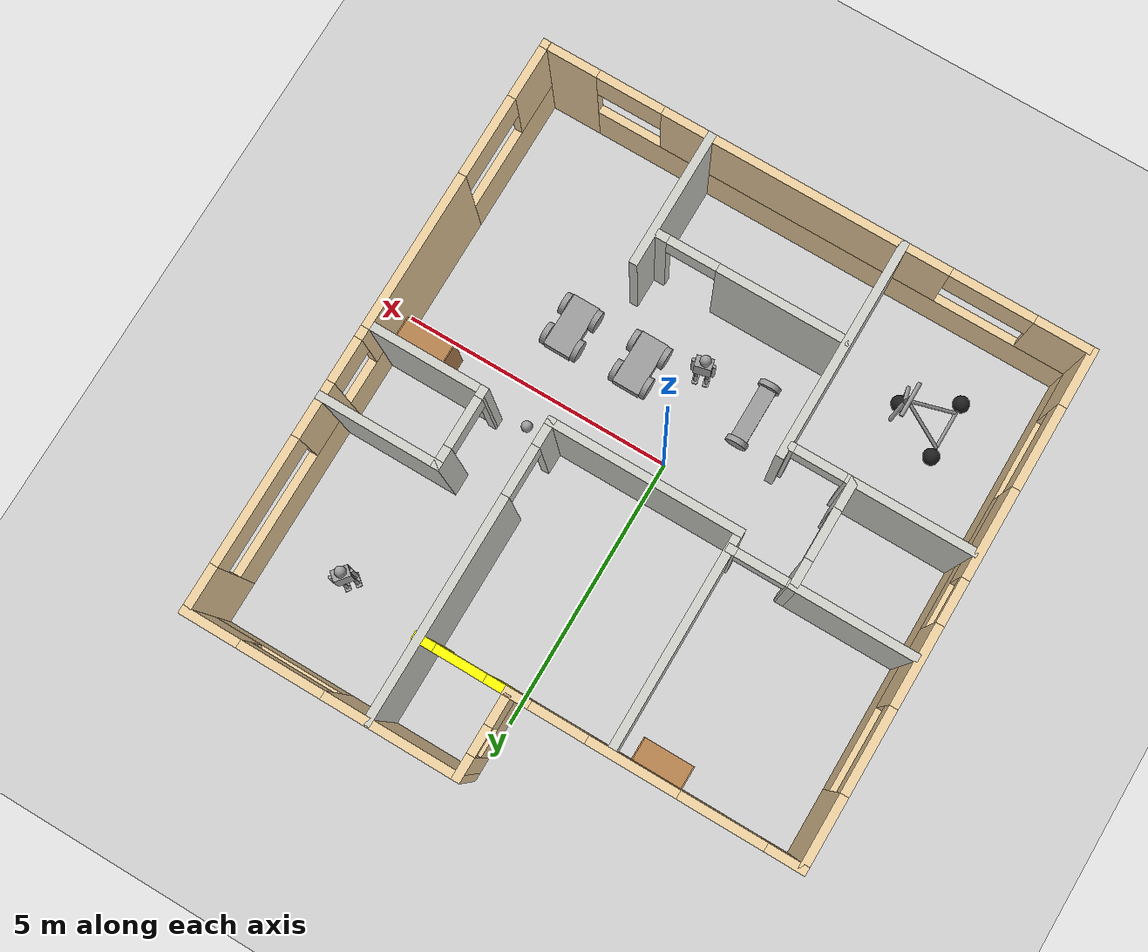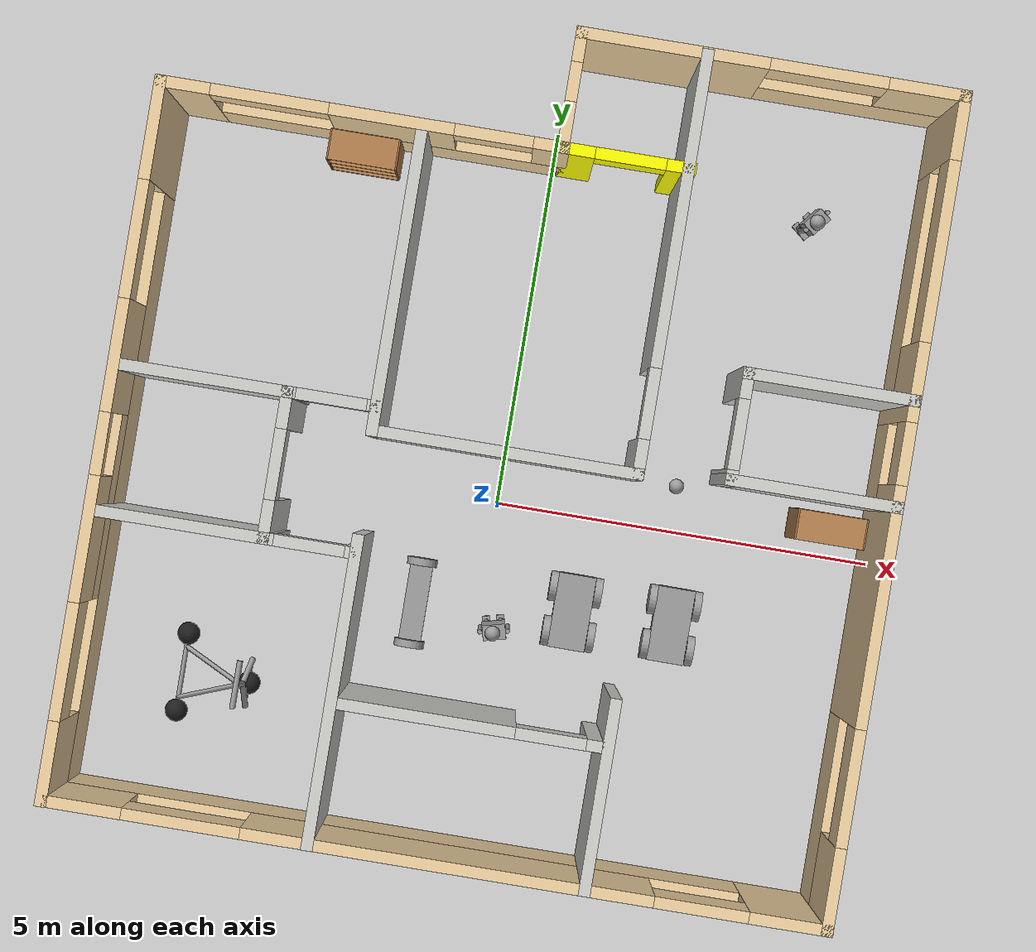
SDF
<sdf version="1.7">
 <world name="default">
  <light name="sun" type="directional">
   <pose>0 0 10 0 -0 0</pose>
   <diffuse>0.8 0.8 0.8 1</diffuse>
   <specular>0.2 0.2 0.2 1</specular>
   <attenuation>
    <range>1000</range>
    <constant>0.9</constant>
    <linear>0.01</linear>
    <quadratic>0.001</quadratic>
   </attenuation>
   <direction>-0.5 0.1 -0.9</direction>
   <spot><inner_angle>0</inner_angle><outer_angle>0</outer_angle><falloff>0</falloff></spot>
  </light>
  <model name="ground_plane">
   <static>1</static>
   <link name="link">
    <collision name="collision">
     <geometry><plane><normal>0 0 1</normal><size>100 100</size></plane></geometry>
     <surface>
      <contact><collide_bitmask>65535</collide_bitmask></contact>
      <friction><ode><mu>100</mu><mu2>50</mu2></ode></friction>
     </surface>
    </collision>
    <visual name="visual">
     <cast_shadows>0</cast_shadows>
     <geometry><plane><normal>0 0 1</normal><size>100 100</size></plane></geometry>
     <material>
      <script><uri>file://media/materials/scripts/gazebo.material</uri><name>Gazebo/Grey</name></script>
     </material>
    </visual>
   </link>
  </model>
  <gravity>0 0 -9.8</gravity>
  <magnetic_field>6e-06 2.3e-05 -4.2e-05</magnetic_field>
  <atmosphere type="adiabatic"/>
  <physics type="ode">
   <max_step_size>0.001</max_step_size>
   <real_time_factor>1</real_time_factor>
   <real_time_update_rate>1000</real_time_update_rate>
  </physics>
  <scene><ambient>0.4 0.4 0.4 1</ambient><background>0.7 0.7 0.7 1</background><shadows>1</shadows></scene>
  <spherical_coordinates>
   <surface_model>EARTH_WGS84</surface_model>
   <latitude_deg>0</latitude_deg>
   <longitude_deg>0</longitude_deg>
   <elevation>0</elevation>
   <heading_deg>0</heading_deg>
  </spherical_coordinates>
  <model name="house">
   <pose>-0.04268 0.71028 0 0 -0 0</pose>
   <link name="Wall_107">
    <collision name="Wall_107_Collision">
     <geometry><box><size>2.5 0.15 2.5</size></box></geometry>
     <pose>0 0 1.25 0 -0 0</pose>
    </collision>
    <visual name="Wall_107_Visual">
     <pose>0 0 1.25 0 -0 0</pose>
     <geometry><box><size>2.5 0.15 2.5</size></box></geometry>
     <material>
      <script><uri>file://media/materials/scripts/gazebo.material</uri><name>Gazebo/CeilingTiled</name></script>
      <ambient>1 1 0 1</ambient>
     </material>
     <meta><layer>0</layer></meta>
    </visual>
    <pose>1.9029 -4.09927 0 0 -0 -1.5708</pose>
   </link>
   <link name="Wall_109">
    <collision name="Wall_109_Collision">
     <geometry><box><size>4 0.15 2.5</size></box></geometry>
     <pose>0 0 1.25 0 -0 0</pose>
    </collision>
    <visual name="Wall_109_Visual">
     <pose>0 0 1.25 0 -0 0</pose>
     <geometry><box><size>4 0.15 2.5</size></box></geometry>
     <material>
      <script><uri>file://media/materials/scripts/gazebo.material</uri><name>Gazebo/CeilingTiled</name></script>
      <ambient>1 1 0 1</ambient>
     </material>
     <meta><layer>0</layer></meta>
    </visual>
    <pose>-1.60432 -3.35052 0 0 -0 1.5708</pose>
   </link>
   <link name="Wall_120">
    <pose>-4.9695 -0.7265 0 0 -0 -1.5708</pose>
    <visual name="Wall_120_Visual_0">
     <pose>-3.96516 0 1.25 0 -0 0</pose>
     <geometry><box><size>1.31967 0.15 2.5</size></box></geometry>
     <material>
      <script><uri>file://media/materials/scripts/gazebo.material</uri><name>Gazebo/Grey</name></script>
      <ambient>0.921569 0.807843 0.615686 1</ambient>
     </material>
     <meta><layer>0</layer></meta>
    </visual>
    <collision name="Wall_120_Collision_0">
     <geometry><box><size>1.31967 0.15 2.5</size></box></geometry>
     <pose>-3.96516 0 1.25 0 -0 0</pose>
    </collision>
    <visual name="Wall_120_Visual_1">
     <pose>0.659837 0 0.5 0 -0 0</pose>
     <geometry><box><size>7.93032 0.15 1</size></box></geometry>
     <material>
      <script><uri>file://media/materials/scripts/gazebo.material</uri><name>Gazebo/Grey</name></script>
      <ambient>0.921569 0.807843 0.615686 1</ambient>
     </material>
     <meta><layer>0</layer></meta>
    </visual>
    <collision name="Wall_120_Collision_1">
     <geometry><box><size>7.93032 0.15 1</size></box></geometry>
     <pose>0.659837 0 0.5 0 -0 0</pose>
    </collision>
    <visual name="Wall_120_Visual_2">
     <pose>-1.08602 0 1.75 0 -0 0</pose>
     <geometry><box><size>1.4386 0.15 1.5</size></box></geometry>
     <material>
      <script><uri>file://media/materials/scripts/gazebo.material</uri><name>Gazebo/Grey</name></script>
      <ambient>0.921569 0.807843 0.615686 1</ambient>
     </material>
     <meta><layer>0</layer></meta>
    </visual>
    <collision name="Wall_120_Collision_2">
     <geometry><box><size>1.4386 0.15 1.5</size></box></geometry>
     <pose>-1.08602 0 1.75 0 -0 0</pose>
    </collision>
    <visual name="Wall_120_Visual_3">
     <pose>4.08435 0 1.75 0 -0 0</pose>
     <geometry><box><size>1.0813 0.15 1.5</size></box></geometry>
     <material>
      <script><uri>file://media/materials/scripts/gazebo.material</uri><name>Gazebo/Grey</name></script>
      <ambient>0.921569 0.807843 0.615686 1</ambient>
     </material>
     <meta><layer>0</layer></meta>
    </visual>
    <collision name="Wall_120_Collision_3">
     <geometry><box><size>1.0813 0.15 1.5</size></box></geometry>
     <pose>4.08435 0 1.75 0 -0 0</pose>
    </collision>
    <visual name="Wall_120_Visual_4">
     <pose>0.838487 0 1.25 0 -0 0</pose>
     <geometry><box><size>2.41042 0.15 0.5</size></box></geometry>
     <material>
      <script><uri>file://media/materials/scripts/gazebo.material</uri><name>Gazebo/Grey</name></script>
      <ambient>0.921569 0.807843 0.615686 1</ambient>
     </material>
     <meta><layer>0</layer></meta>
    </visual>
    <collision name="Wall_120_Collision_4">
     <geometry><box><size>2.41042 0.15 0.5</size></box></geometry>
     <pose>0.838487 0 1.25 0 -0 0</pose>
    </collision>
    <visual name="Wall_120_Visual_5">
     <pose>2.7937 0 1 0 -0 0</pose>
     <geometry><box><size>1.5 0.15 0</size></box></geometry>
     <material>
      <script><uri>file://media/materials/scripts/gazebo.material</uri><name>Gazebo/Grey</name></script>
      <ambient>0.921569 0.807843 0.615686 1</ambient>
     </material>
     <meta><layer>0</layer></meta>
    </visual>
    <collision name="Wall_120_Collision_5">
     <geometry><box><size>1.5 0.15 0</size></box></geometry>
     <pose>2.7937 0 1 0 -0 0</pose>
    </collision>
    <visual name="Wall_120_Visual_6">
     <pose>1.23849 0 2 0 -0 0</pose>
     <geometry><box><size>1.61042 0.15 1</size></box></geometry>
     <material>
      <script><uri>file://media/materials/scripts/gazebo.material</uri><name>Gazebo/Grey</name></script>
      <ambient>0.921569 0.807843 0.615686 1</ambient>
     </material>
     <meta><layer>0</layer></meta>
    </visual>
    <collision name="Wall_120_Collision_6">
     <geometry><box><size>1.61042 0.15 1</size></box></geometry>
     <pose>1.23849 0 2 0 -0 0</pose>
    </collision>
    <visual name="Wall_120_Visual_7">
     <pose>2.7937 0 2.15 0 -0 0</pose>
     <geometry><box><size>1.5 0.15 0.7</size></box></geometry>
     <material>
      <script><uri>file://media/materials/scripts/gazebo.material</uri><name>Gazebo/Grey</name></script>
      <ambient>0.921569 0.807843 0.615686 1</ambient>
     </material>
     <meta><layer>0</layer></meta>
    </visual>
    <collision name="Wall_120_Collision_7">
     <geometry><box><size>1.5 0.15 0.7</size></box></geometry>
     <pose>2.7937 0 2.15 0 -0 0</pose>
    </collision>
    <visual name="Wall_120_Visual_8">
     <pose>-2.55532 0 2.25 0 -0 0</pose>
     <geometry><box><size>1.5 0.15 0.5</size></box></geometry>
     <material>
      <script><uri>file://media/materials/scripts/gazebo.material</uri><name>Gazebo/Grey</name></script>
      <ambient>0.921569 0.807843 0.615686 1</ambient>
     </material>
     <meta><layer>0</layer></meta>
    </visual>
    <collision name="Wall_120_Collision_8">
     <geometry><box><size>1.5 0.15 0.5</size></box></geometry>
     <pose>-2.55532 0 2.25 0 -0 0</pose>
    </collision>
    <visual name="Wall_120_Visual_9">
     <pose>0.033278 0 2.4 0 -0 0</pose>
     <geometry><box><size>0.8 0.15 0.2</size></box></geometry>
     <material>
      <script><uri>file://media/materials/scripts/gazebo.material</uri><name>Gazebo/Grey</name></script>
      <ambient>0.921569 0.807843 0.615686 1</ambient>
     </material>
     <meta><layer>0</layer></meta>
    </visual>
    <collision name="Wall_120_Collision_9">
     <geometry><box><size>0.8 0.15 0.2</size></box></geometry>
     <pose>0.033278 0 2.4 0 -0 0</pose>
    </collision>
   </link>
   <link name="Wall_131">
    <pose>-2.774 -0.669222 0 0 -0 1.5708</pose>
    <visual name="Wall_131_Visual_0">
     <pose>-0.72 0 1.25 0 -0 0</pose>
     <geometry><box><size>0.559999 0.15 2.5</size></box></geometry>
     <material>
      <script><uri>file://media/materials/scripts/gazebo.material</uri><name>Gazebo/CeilingTiled</name></script>
      <ambient>1 1 0 1</ambient>
     </material>
     <meta><layer>0</layer></meta>
    </visual>
    <collision name="Wall_131_Collision_0">
     <geometry><box><size>0.559999 0.15 2.5</size></box></geometry>
     <pose>-0.72 0 1.25 0 -0 0</pose>
    </collision>
    <visual name="Wall_131_Visual_1">
     <pose>0.73 0 1.25 0 -0 0</pose>
     <geometry><box><size>0.540001 0.15 2.5</size></box></geometry>
     <material>
      <script><uri>file://media/materials/scripts/gazebo.material</uri><name>Gazebo/CeilingTiled</name></script>
      <ambient>1 1 0 1</ambient>
     </material>
     <meta><layer>0</layer></meta>
    </visual>
    <collision name="Wall_131_Collision_1">
     <geometry><box><size>0.540001 0.15 2.5</size></box></geometry>
     <pose>0.73 0 1.25 0 -0 0</pose>
    </collision>
    <visual name="Wall_131_Visual_2">
     <pose>0.009999 0 2.25 0 -0 0</pose>
     <geometry><box><size>0.9 0.15 0.5</size></box></geometry>
     <material>
      <script><uri>file://media/materials/scripts/gazebo.material</uri><name>Gazebo/CeilingTiled</name></script>
      <ambient>1 1 0 1</ambient>
     </material>
     <meta><layer>0</layer></meta>
    </visual>
    <collision name="Wall_131_Collision_2">
     <geometry><box><size>0.9 0.15 0.5</size></box></geometry>
     <pose>0.009999 0 2.25 0 -0 0</pose>
    </collision>
   </link>
   <link name="Wall_132">
    <collision name="Wall_132_Collision">
     <geometry><box><size>2.25 0.15 2.5</size></box></geometry>
     <pose>0 0 1.25 0 -0 0</pose>
    </collision>
    <visual name="Wall_132_Visual">
     <pose>0 0 1.25 0 -0 0</pose>
     <geometry><box><size>2.25 0.15 2.5</size></box></geometry>
     <material>
      <script><uri>file://media/materials/scripts/gazebo.material</uri><name>Gazebo/CeilingTiled</name></script>
      <ambient>1 1 0 1</ambient>
     </material>
     <meta><layer>0</layer></meta>
    </visual>
    <pose>-3.824 0.255778 0 0 -0 3.14159</pose>
   </link>
   <link name="Wall_137">
    <pose>-2.4195 3.8235 0 0 -0 0</pose>
    <visual name="Wall_137_Visual_0">
     <pose>-2.27291 0 1.25 0 -0 0</pose>
     <geometry><box><size>0.70419 0.15 2.5</size></box></geometry>
     <material>
      <script><uri>file://media/materials/scripts/gazebo.material</uri><name>Gazebo/Grey</name></script>
      <ambient>0.921569 0.807843 0.615686 1</ambient>
     </material>
     <meta><layer>0</layer></meta>
    </visual>
    <collision name="Wall_137_Collision_0">
     <geometry><box><size>0.70419 0.15 2.5</size></box></geometry>
     <pose>-2.27291 0 1.25 0 -0 0</pose>
    </collision>
    <visual name="Wall_137_Visual_1">
     <pose>0.352095 0 0.5 0 -0 0</pose>
     <geometry><box><size>4.54581 0.15 1</size></box></geometry>
     <material>
      <script><uri>file://media/materials/scripts/gazebo.material</uri><name>Gazebo/Grey</name></script>
      <ambient>0.921569 0.807843 0.615686 1</ambient>
     </material>
     <meta><layer>0</layer></meta>
    </visual>
    <collision name="Wall_137_Collision_1">
     <geometry><box><size>4.54581 0.15 1</size></box></geometry>
     <pose>0.352095 0 0.5 0 -0 0</pose>
    </collision>
    <visual name="Wall_137_Visual_2">
     <pose>0.373282 0 1.75 0 -0 0</pose>
     <geometry><box><size>1.58818 0.15 1.5</size></box></geometry>
     <material>
      <script><uri>file://media/materials/scripts/gazebo.material</uri><name>Gazebo/Grey</name></script>
      <ambient>0.921569 0.807843 0.615686 1</ambient>
     </material>
     <meta><layer>0</layer></meta>
    </visual>
    <collision name="Wall_137_Collision_2">
     <geometry><box><size>1.58818 0.15 1.5</size></box></geometry>
     <pose>0.373282 0 1.75 0 -0 0</pose>
    </collision>
    <visual name="Wall_137_Visual_3">
     <pose>2.39619 0 1.75 0 -0 0</pose>
     <geometry><box><size>0.457627 0.15 1.5</size></box></geometry>
     <material>
      <script><uri>file://media/materials/scripts/gazebo.material</uri><name>Gazebo/Grey</name></script>
      <ambient>0.921569 0.807843 0.615686 1</ambient>
     </material>
     <meta><layer>0</layer></meta>
    </visual>
    <collision name="Wall_137_Collision_3">
     <geometry><box><size>0.457627 0.15 1.5</size></box></geometry>
     <pose>2.39619 0 1.75 0 -0 0</pose>
    </collision>
    <visual name="Wall_137_Visual_4">
     <pose>-1.17081 0 2.25 0 -0 0</pose>
     <geometry><box><size>1.5 0.15 0.5</size></box></geometry>
     <material>
      <script><uri>file://media/materials/scripts/gazebo.material</uri><name>Gazebo/Grey</name></script>
      <ambient>0.921569 0.807843 0.615686 1</ambient>
     </material>
     <meta><layer>0</layer></meta>
    </visual>
    <collision name="Wall_137_Collision_4">
     <geometry><box><size>1.5 0.15 0.5</size></box></geometry>
     <pose>-1.17081 0 2.25 0 -0 0</pose>
    </collision>
    <visual name="Wall_137_Visual_5">
     <pose>1.66737 0 2.25 0 -0 0</pose>
     <geometry><box><size>1 0.15 0.5</size></box></geometry>
     <material>
      <script><uri>file://media/materials/scripts/gazebo.material</uri><name>Gazebo/Grey</name></script>
      <ambient>0.921569 0.807843 0.615686 1</ambient>
     </material>
     <meta><layer>0</layer></meta>
    </visual>
    <collision name="Wall_137_Collision_5">
     <geometry><box><size>1 0.15 0.5</size></box></geometry>
     <pose>1.66737 0 2.25 0 -0 0</pose>
    </collision>
   </link>
   <link name="Wall_142">
    <pose>0.094094 -3.47845 0 0 -0 0</pose>
    <visual name="Wall_142_Visual_0">
     <pose>-0.559233 0 1.25 0 -0 0</pose>
     <geometry><box><size>2.38153 0.15 2.5</size></box></geometry>
     <material>
      <script><uri>file://media/materials/scripts/gazebo.material</uri><name>Gazebo/CeilingTiled</name></script>
      <ambient>1 1 0 1</ambient>
     </material>
     <meta><layer>0</layer></meta>
    </visual>
    <collision name="Wall_142_Collision_0">
     <geometry><box><size>2.38153 0.15 2.5</size></box></geometry>
     <pose>-0.559233 0 1.25 0 -0 0</pose>
    </collision>
    <visual name="Wall_142_Visual_1">
     <pose>1.64077 0 1.25 0 -0 0</pose>
     <geometry><box><size>0.218467 0.15 2.5</size></box></geometry>
     <material>
      <script><uri>file://media/materials/scripts/gazebo.material</uri><name>Gazebo/CeilingTiled</name></script>
      <ambient>1 1 0 1</ambient>
     </material>
     <meta><layer>0</layer></meta>
    </visual>
    <collision name="Wall_142_Collision_1">
     <geometry><box><size>0.218467 0.15 2.5</size></box></geometry>
     <pose>1.64077 0 1.25 0 -0 0</pose>
    </collision>
    <visual name="Wall_142_Visual_2">
     <pose>1.08153 0 2.25 0 -0 0</pose>
     <geometry><box><size>0.9 0.15 0.5</size></box></geometry>
     <material>
      <script><uri>file://media/materials/scripts/gazebo.material</uri><name>Gazebo/CeilingTiled</name></script>
      <ambient>1 1 0 1</ambient>
     </material>
     <meta><layer>0</layer></meta>
    </visual>
    <collision name="Wall_142_Collision_2">
     <geometry><box><size>0.9 0.15 0.5</size></box></geometry>
     <pose>1.08153 0 2.25 0 -0 0</pose>
    </collision>
   </link>
   <link name="Wall_144">
    <pose>-2.224 -1.59422 0 0 -0 0</pose>
    <visual name="Wall_144_Visual_0">
     <pose>-0.522492 0 1.25 0 -0 0</pose>
     <geometry><box><size>0.205015 0.15 2.5</size></box></geometry>
     <material>
      <script><uri>file://media/materials/scripts/gazebo.material</uri><name>Gazebo/CeilingTiled</name></script>
      <ambient>1 1 0 1</ambient>
     </material>
     <meta><layer>0</layer></meta>
    </visual>
    <collision name="Wall_144_Collision_0">
     <geometry><box><size>0.205015 0.15 2.5</size></box></geometry>
     <pose>-0.522492 0 1.25 0 -0 0</pose>
    </collision>
    <visual name="Wall_144_Visual_1">
     <pose>0.552508 0 1.25 0 -0 0</pose>
     <geometry><box><size>0.144985 0.15 2.5</size></box></geometry>
     <material>
      <script><uri>file://media/materials/scripts/gazebo.material</uri><name>Gazebo/CeilingTiled</name></script>
      <ambient>1 1 0 1</ambient>
     </material>
     <meta><layer>0</layer></meta>
    </visual>
    <collision name="Wall_144_Collision_1">
     <geometry><box><size>0.144985 0.15 2.5</size></box></geometry>
     <pose>0.552508 0 1.25 0 -0 0</pose>
    </collision>
    <visual name="Wall_144_Visual_2">
     <pose>0.030015 0 2.25 0 -0 0</pose>
     <geometry><box><size>0.9 0.15 0.5</size></box></geometry>
     <material>
      <script><uri>file://media/materials/scripts/gazebo.material</uri><name>Gazebo/CeilingTiled</name></script>
      <ambient>1 1 0 1</ambient>
     </material>
     <meta><layer>0</layer></meta>
    </visual>
    <collision name="Wall_144_Collision_2">
     <geometry><box><size>0.9 0.15 0.5</size></box></geometry>
     <pose>0.030015 0 2.25 0 -0 0</pose>
    </collision>
   </link>
   <link name="Wall_148">
    <pose>-2.224 0.255778 0 0 -0 0</pose>
    <visual name="Wall_148_Visual_0">
     <pose>-0.534251 0 1.25 0 -0 0</pose>
     <geometry><box><size>0.181499 0.15 2.5</size></box></geometry>
     <material>
      <script><uri>file://media/materials/scripts/gazebo.material</uri><name>Gazebo/CeilingTiled</name></script>
      <ambient>1 1 0 1</ambient>
     </material>
     <meta><layer>0</layer></meta>
    </visual>
    <collision name="Wall_148_Collision_0">
     <geometry><box><size>0.181499 0.15 2.5</size></box></geometry>
     <pose>-0.534251 0 1.25 0 -0 0</pose>
    </collision>
    <visual name="Wall_148_Visual_1">
     <pose>0.540749 0 1.25 0 -0 0</pose>
     <geometry><box><size>0.168501 0.15 2.5</size></box></geometry>
     <material>
      <script><uri>file://media/materials/scripts/gazebo.material</uri><name>Gazebo/CeilingTiled</name></script>
      <ambient>1 1 0 1</ambient>
     </material>
     <meta><layer>0</layer></meta>
    </visual>
    <collision name="Wall_148_Collision_1">
     <geometry><box><size>0.168501 0.15 2.5</size></box></geometry>
     <pose>0.540749 0 1.25 0 -0 0</pose>
    </collision>
    <visual name="Wall_148_Visual_2">
     <pose>0.006499 0 2.25 0 -0 0</pose>
     <geometry><box><size>0.9 0.15 0.5</size></box></geometry>
     <material>
      <script><uri>file://media/materials/scripts/gazebo.material</uri><name>Gazebo/CeilingTiled</name></script>
      <ambient>1 1 0 1</ambient>
     </material>
     <meta><layer>0</layer></meta>
    </visual>
    <collision name="Wall_148_Collision_2">
     <geometry><box><size>0.9 0.15 0.5</size></box></geometry>
     <pose>0.006499 0 2.25 0 -0 0</pose>
    </collision>
   </link>
   <link name="Wall_159">
    <pose>1.7115 2.606 0 0 -0 1.5708</pose>
    <visual name="Wall_159_Visual_0">
     <pose>-2.465 0 1.25 0 -0 0</pose>
     <geometry><box><size>0.520748 0.15 2.5</size></box></geometry>
     <material>
      <script><uri>file://media/materials/scripts/gazebo.material</uri><name>Gazebo/CeilingTiled</name></script>
      <ambient>1 1 0 1</ambient>
     </material>
     <meta><layer>0</layer></meta>
    </visual>
    <collision name="Wall_159_Collision_0">
     <geometry><box><size>0.520748 0.15 2.5</size></box></geometry>
     <pose>-2.465 0 1.25 0 -0 0</pose>
    </collision>
    <visual name="Wall_159_Visual_1">
     <pose>0.710374 0 1.25 0 -0 0</pose>
     <geometry><box><size>4.02999 0.15 2.5</size></box></geometry>
     <material>
      <script><uri>file://media/materials/scripts/gazebo.material</uri><name>Gazebo/CeilingTiled</name></script>
      <ambient>1 1 0 1</ambient>
     </material>
     <meta><layer>0</layer></meta>
    </visual>
    <collision name="Wall_159_Collision_1">
     <geometry><box><size>4.02999 0.15 2.5</size></box></geometry>
     <pose>0.710374 0 1.25 0 -0 0</pose>
    </collision>
    <visual name="Wall_159_Visual_2">
     <pose>-1.75462 0 2.25 0 -0 0</pose>
     <geometry><box><size>0.9 0.15 0.5</size></box></geometry>
     <material>
      <script><uri>file://media/materials/scripts/gazebo.material</uri><name>Gazebo/CeilingTiled</name></script>
      <ambient>1 1 0 1</ambient>
     </material>
     <meta><layer>0</layer></meta>
    </visual>
    <collision name="Wall_159_Collision_2">
     <geometry><box><size>0.9 0.15 0.5</size></box></geometry>
     <pose>-1.75462 0 2.25 0 -0 0</pose>
    </collision>
   </link>
   <link name="Wall_161">
    <pose>0.9305 3.8235 0 0 -0 0</pose>
    <visual name="Wall_161_Visual_0">
     <pose>-0.637254 0 1.25 0 -0 0</pose>
     <geometry><box><size>0.475492 0.15 2.5</size></box></geometry>
     <material>
      <script><uri>file://media/materials/scripts/gazebo.material</uri><name>Gazebo/Grey</name></script>
      <ambient>1 1 0 1</ambient>
     </material>
     <meta><layer>0</layer></meta>
    </visual>
    <collision name="Wall_161_Collision_0">
     <geometry><box><size>0.475492 0.15 2.5</size></box></geometry>
     <pose>-0.637254 0 1.25 0 -0 0</pose>
    </collision>
    <visual name="Wall_161_Visual_1">
     <pose>0.687746 0 1.25 0 -0 0</pose>
     <geometry><box><size>0.374508 0.15 2.5</size></box></geometry>
     <material>
      <script><uri>file://media/materials/scripts/gazebo.material</uri><name>Gazebo/Grey</name></script>
      <ambient>1 1 0 1</ambient>
     </material>
     <meta><layer>0</layer></meta>
    </visual>
    <collision name="Wall_161_Collision_1">
     <geometry><box><size>0.374508 0.15 2.5</size></box></geometry>
     <pose>0.687746 0 1.25 0 -0 0</pose>
    </collision>
    <visual name="Wall_161_Visual_2">
     <pose>0.050492 0 2.25 0 -0 0</pose>
     <geometry><box><size>0.9 0.15 0.5</size></box></geometry>
     <material>
      <script><uri>file://media/materials/scripts/gazebo.material</uri><name>Gazebo/Grey</name></script>
      <ambient>1 1 0 1</ambient>
     </material>
     <meta><layer>0</layer></meta>
    </visual>
    <collision name="Wall_161_Collision_2">
     <geometry><box><size>0.9 0.15 0.5</size></box></geometry>
     <pose>0.050492 0 2.25 0 -0 0</pose>
    </collision>
   </link>
   <link name="Wall_38">
    <pose>2.5445 5.2765 0 0 -0 0</pose>
    <visual name="Wall_38_Visual_0">
     <pose>-1.27127 0 1.25 0 -0 0</pose>
     <geometry><box><size>2.45747 0.15 2.5</size></box></geometry>
     <material>
      <script><uri>file://media/materials/scripts/gazebo.material</uri><name>Gazebo/Grey</name></script>
      <ambient>0.921569 0.807843 0.615686 1</ambient>
     </material>
     <meta><layer>0</layer></meta>
    </visual>
    <collision name="Wall_38_Collision_0">
     <geometry><box><size>2.45747 0.15 2.5</size></box></geometry>
     <pose>-1.27127 0 1.25 0 -0 0</pose>
    </collision>
    <visual name="Wall_38_Visual_1">
     <pose>1.22873 0 0.5 0 -0 0</pose>
     <geometry><box><size>2.54253 0.15 1</size></box></geometry>
     <material>
      <script><uri>file://media/materials/scripts/gazebo.material</uri><name>Gazebo/Grey</name></script>
      <ambient>0.921569 0.807843 0.615686 1</ambient>
     </material>
     <meta><layer>0</layer></meta>
    </visual>
    <collision name="Wall_38_Collision_1">
     <geometry><box><size>2.54253 0.15 1</size></box></geometry>
     <pose>1.22873 0 0.5 0 -0 0</pose>
    </collision>
    <visual name="Wall_38_Visual_2">
     <pose>1.97873 0 1.75 0 -0 0</pose>
     <geometry><box><size>1.04253 0.15 1.5</size></box></geometry>
     <material>
      <script><uri>file://media/materials/scripts/gazebo.material</uri><name>Gazebo/Grey</name></script>
      <ambient>0.921569 0.807843 0.615686 1</ambient>
     </material>
     <meta><layer>0</layer></meta>
    </visual>
    <collision name="Wall_38_Collision_2">
     <geometry><box><size>1.04253 0.15 1.5</size></box></geometry>
     <pose>1.97873 0 1.75 0 -0 0</pose>
    </collision>
    <visual name="Wall_38_Visual_3">
     <pose>0.707471 0 2.15 0 -0 0</pose>
     <geometry><box><size>1.5 0.15 0.7</size></box></geometry>
     <material>
      <script><uri>file://media/materials/scripts/gazebo.material</uri><name>Gazebo/Grey</name></script>
      <ambient>0.921569 0.807843 0.615686 1</ambient>
     </material>
     <meta><layer>0</layer></meta>
    </visual>
    <collision name="Wall_38_Collision_3">
     <geometry><box><size>1.5 0.15 0.7</size></box></geometry>
     <pose>0.707471 0 2.15 0 -0 0</pose>
    </collision>
   </link>
   <link name="Wall_59">
    <collision name="Wall_59_Collision">
     <geometry><box><size>2.25 0.15 2.5</size></box></geometry>
     <pose>0 0 1.25 0 -0 0</pose>
    </collision>
    <visual name="Wall_59_Visual">
     <pose>0 0 1.25 0 -0 0</pose>
     <geometry><box><size>2.25 0.15 2.5</size></box></geometry>
     <material>
      <script><uri>file://media/materials/scripts/gazebo.material</uri><name>Gazebo/CeilingTiled</name></script>
      <ambient>1 1 0 1</ambient>
     </material>
     <meta><layer>0</layer></meta>
    </visual>
    <pose>-3.824 -1.59422 0 0 -0 3.14159</pose>
   </link>
   <link name="Wall_62">
    <pose>0.1195 4.6015 0 0 -0 -1.5708</pose>
    <visual name="Wall_62_Visual_0">
     <pose>-0.527407 0 1.25 0 -0 0</pose>
     <geometry><box><size>0.445186 0.15 2.5</size></box></geometry>
     <material>
      <script><uri>file://media/materials/scripts/gazebo.material</uri><name>Gazebo/Grey</name></script>
      <ambient>0.921569 0.807843 0.615686 1</ambient>
     </material>
     <meta><layer>0</layer></meta>
    </visual>
    <collision name="Wall_62_Collision_0">
     <geometry><box><size>0.445186 0.15 2.5</size></box></geometry>
     <pose>-0.527407 0 1.25 0 -0 0</pose>
    </collision>
    <visual name="Wall_62_Visual_1">
     <pose>0.222593 0 0.75 0 -0 0</pose>
     <geometry><box><size>1.05481 0.15 1.5</size></box></geometry>
     <material>
      <script><uri>file://media/materials/scripts/gazebo.material</uri><name>Gazebo/Grey</name></script>
      <ambient>0.921569 0.807843 0.615686 1</ambient>
     </material>
     <meta><layer>0</layer></meta>
    </visual>
    <collision name="Wall_62_Collision_1">
     <geometry><box><size>1.05481 0.15 1.5</size></box></geometry>
     <pose>0.222593 0 0.75 0 -0 0</pose>
    </collision>
    <visual name="Wall_62_Visual_2">
     <pose>0.472593 0 2 0 -0 0</pose>
     <geometry><box><size>0.554814 0.15 1</size></box></geometry>
     <material>
      <script><uri>file://media/materials/scripts/gazebo.material</uri><name>Gazebo/Grey</name></script>
      <ambient>0.921569 0.807843 0.615686 1</ambient>
     </material>
     <meta><layer>0</layer></meta>
    </visual>
    <collision name="Wall_62_Collision_2">
     <geometry><box><size>0.554814 0.15 1</size></box></geometry>
     <pose>0.472593 0 2 0 -0 0</pose>
    </collision>
    <visual name="Wall_62_Visual_3">
     <pose>-0.054814 0 2.4 0 -0 0</pose>
     <geometry><box><size>0.5 0.15 0.2</size></box></geometry>
     <material>
      <script><uri>file://media/materials/scripts/gazebo.material</uri><name>Gazebo/Grey</name></script>
      <ambient>0.921569 0.807843 0.615686 1</ambient>
     </material>
     <meta><layer>0</layer></meta>
    </visual>
    <collision name="Wall_62_Collision_3">
     <geometry><box><size>0.5 0.15 0.2</size></box></geometry>
     <pose>-0.054814 0 2.4 0 -0 0</pose>
    </collision>
   </link>
   <link name="Wall_69">
    <collision name="Wall_69_Collision">
     <geometry><box><size>3.99291 0.15 2.5</size></box></geometry>
     <pose>0 0 1.25 0 -0 0</pose>
    </collision>
    <visual name="Wall_69_Visual">
     <pose>0 0 1.25 0 -0 0</pose>
     <geometry><box><size>3.99291 0.15 2.5</size></box></geometry>
     <material>
      <script><uri>file://media/materials/scripts/gazebo.material</uri><name>Gazebo/CeilingTiled</name></script>
      <ambient>1 1 0 1</ambient>
     </material>
     <meta><layer>0</layer></meta>
    </visual>
    <pose>-1.65193 1.87737 0 0 -0 -1.5708</pose>
   </link>
   <link name="Wall_70">
    <collision name="Wall_70_Collision">
     <geometry><box><size>3.51343 0.15 2.5</size></box></geometry>
     <pose>0 0 1.25 0 -0 0</pose>
    </collision>
    <visual name="Wall_70_Visual">
     <pose>0 0 1.25 0 -0 0</pose>
     <geometry><box><size>3.51343 0.15 2.5</size></box></geometry>
     <material>
      <script><uri>file://media/materials/scripts/gazebo.material</uri><name>Gazebo/CeilingTiled</name></script>
      <ambient>1 1 0 1</ambient>
     </material>
     <meta><layer>0</layer></meta>
    </visual>
    <pose>0.029785 -0.044292 0 0 -0 -0.000123</pose>
   </link>
   <link name="Wall_75">
    <pose>4.9695 3.3515 0 0 -0 -1.5708</pose>
    <visual name="Wall_75_Visual_0">
     <pose>-1.55726 0 1.25 0 -0 0</pose>
     <geometry><box><size>0.885485 0.15 2.5</size></box></geometry>
     <material>
      <script><uri>file://media/materials/scripts/gazebo.material</uri><name>Gazebo/Grey</name></script>
      <ambient>0.921569 0.807843 0.615686 1</ambient>
     </material>
     <meta><layer>0</layer></meta>
    </visual>
    <collision name="Wall_75_Collision_0">
     <geometry><box><size>0.885485 0.15 2.5</size></box></geometry>
     <pose>-1.55726 0 1.25 0 -0 0</pose>
    </collision>
    <visual name="Wall_75_Visual_1">
     <pose>0.442742 0 0.5 0 -0 0</pose>
     <geometry><box><size>3.11451 0.15 1</size></box></geometry>
     <material>
      <script><uri>file://media/materials/scripts/gazebo.material</uri><name>Gazebo/Grey</name></script>
      <ambient>0.921569 0.807843 0.615686 1</ambient>
     </material>
     <meta><layer>0</layer></meta>
    </visual>
    <collision name="Wall_75_Collision_1">
     <geometry><box><size>3.11451 0.15 1</size></box></geometry>
     <pose>0.442742 0 0.5 0 -0 0</pose>
    </collision>
    <visual name="Wall_75_Visual_2">
     <pose>1.59274 0 1.75 0 -0 0</pose>
     <geometry><box><size>0.814515 0.15 1.5</size></box></geometry>
     <material>
      <script><uri>file://media/materials/scripts/gazebo.material</uri><name>Gazebo/Grey</name></script>
      <ambient>0.921569 0.807843 0.615686 1</ambient>
     </material>
     <meta><layer>0</layer></meta>
    </visual>
    <collision name="Wall_75_Collision_2">
     <geometry><box><size>0.814515 0.15 1.5</size></box></geometry>
     <pose>1.59274 0 1.75 0 -0 0</pose>
    </collision>
    <visual name="Wall_75_Visual_3">
     <pose>0.035485 0 2.15 0 -0 0</pose>
     <geometry><box><size>2.3 0.15 0.7</size></box></geometry>
     <material>
      <script><uri>file://media/materials/scripts/gazebo.material</uri><name>Gazebo/Grey</name></script>
      <ambient>0.921569 0.807843 0.615686 1</ambient>
     </material>
     <meta><layer>0</layer></meta>
    </visual>
    <collision name="Wall_75_Collision_3">
     <geometry><box><size>2.3 0.15 0.7</size></box></geometry>
     <pose>0.035485 0 2.15 0 -0 0</pose>
    </collision>
   </link>
   <link name="Wall_78">
    <collision name="Wall_78_Collision">
     <geometry><box><size>2.25 0.15 2.5</size></box></geometry>
     <pose>0 0 1.25 0 -0 0</pose>
    </collision>
    <visual name="Wall_78_Visual">
     <pose>0 0 1.25 0 -0 0</pose>
     <geometry><box><size>2.25 0.15 2.5</size></box></geometry>
     <material>
      <script><uri>file://media/materials/scripts/gazebo.material</uri><name>Gazebo/CeilingTiled</name></script>
      <ambient>1 1 0 1</ambient>
     </material>
     <meta><layer>0</layer></meta>
    </visual>
    <pose>3.9195 1.4265 0 0 -0 3.14159</pose>
   </link>
   <link name="Wall_81">
    <pose>4.9695 0.7515 0 0 -0 -1.5708</pose>
    <visual name="Wall_81_Visual_0">
     <pose>-0.576155 0 1.25 0 -0 0</pose>
     <geometry><box><size>0.347689 0.15 2.5</size></box></geometry>
     <material>
      <script><uri>file://media/materials/scripts/gazebo.material</uri><name>Gazebo/Grey</name></script>
      <ambient>0.921569 0.807843 0.615686 1</ambient>
     </material>
     <meta><layer>0</layer></meta>
    </visual>
    <collision name="Wall_81_Collision_0">
     <geometry><box><size>0.347689 0.15 2.5</size></box></geometry>
     <pose>-0.576155 0 1.25 0 -0 0</pose>
    </collision>
    <visual name="Wall_81_Visual_1">
     <pose>0.173845 0 0.5 0 -0 0</pose>
     <geometry><box><size>1.15231 0.15 1</size></box></geometry>
     <material>
      <script><uri>file://media/materials/scripts/gazebo.material</uri><name>Gazebo/Grey</name></script>
      <ambient>0.921569 0.807843 0.615686 1</ambient>
     </material>
     <meta><layer>0</layer></meta>
    </visual>
    <collision name="Wall_81_Collision_1">
     <geometry><box><size>1.15231 0.15 1</size></box></geometry>
     <pose>0.173845 0 0.5 0 -0 0</pose>
    </collision>
    <visual name="Wall_81_Visual_2">
     <pose>0.573845 0 1.75 0 -0 0</pose>
     <geometry><box><size>0.352311 0.15 1.5</size></box></geometry>
     <material>
      <script><uri>file://media/materials/scripts/gazebo.material</uri><name>Gazebo/Grey</name></script>
      <ambient>0.921569 0.807843 0.615686 1</ambient>
     </material>
     <meta><layer>0</layer></meta>
    </visual>
    <collision name="Wall_81_Collision_2">
     <geometry><box><size>0.352311 0.15 1.5</size></box></geometry>
     <pose>0.573845 0 1.75 0 -0 0</pose>
    </collision>
    <visual name="Wall_81_Visual_3">
     <pose>-0.002311 0 2.15 0 -0 0</pose>
     <geometry><box><size>0.8 0.15 0.7</size></box></geometry>
     <material>
      <script><uri>file://media/materials/scripts/gazebo.material</uri><name>Gazebo/Grey</name></script>
      <ambient>0.921569 0.807843 0.615686 1</ambient>
     </material>
     <meta><layer>0</layer></meta>
    </visual>
    <collision name="Wall_81_Collision_3">
     <geometry><box><size>0.8 0.15 0.7</size></box></geometry>
     <pose>-0.002311 0 2.15 0 -0 0</pose>
    </collision>
   </link>
   <link name="Wall_82">
    <collision name="Wall_82_Collision">
     <geometry><box><size>2.25 0.15 2.5</size></box></geometry>
     <pose>0 0 1.25 0 -0 0</pose>
    </collision>
    <visual name="Wall_82_Visual">
     <pose>0 0 1.25 0 -0 0</pose>
     <geometry><box><size>2.25 0.15 2.5</size></box></geometry>
     <material>
      <script><uri>file://media/materials/scripts/gazebo.material</uri><name>Gazebo/CeilingTiled</name></script>
      <ambient>1 1 0 1</ambient>
     </material>
     <meta><layer>0</layer></meta>
    </visual>
    <pose>3.9195 0.0765 0 0 -0 3.14159</pose>
   </link>
   <link name="Wall_83">
    <pose>2.8695 0.7515 0 0 -0 1.5708</pose>
    <visual name="Wall_83_Visual_0">
     <pose>-0.648933 0 1.25 0 -0 0</pose>
     <geometry><box><size>0.202134 0.15 2.5</size></box></geometry>
     <material>
      <script><uri>file://media/materials/scripts/gazebo.material</uri><name>Gazebo/CeilingTiled</name></script>
      <ambient>1 1 0 1</ambient>
     </material>
     <meta><layer>0</layer></meta>
    </visual>
    <collision name="Wall_83_Collision_0">
     <geometry><box><size>0.202134 0.15 2.5</size></box></geometry>
     <pose>-0.648933 0 1.25 0 -0 0</pose>
    </collision>
    <visual name="Wall_83_Visual_1">
     <pose>0.551067 0 1.25 0 -0 0</pose>
     <geometry><box><size>0.397866 0.15 2.5</size></box></geometry>
     <material>
      <script><uri>file://media/materials/scripts/gazebo.material</uri><name>Gazebo/CeilingTiled</name></script>
      <ambient>1 1 0 1</ambient>
     </material>
     <meta><layer>0</layer></meta>
    </visual>
    <collision name="Wall_83_Collision_1">
     <geometry><box><size>0.397866 0.15 2.5</size></box></geometry>
     <pose>0.551067 0 1.25 0 -0 0</pose>
    </collision>
    <visual name="Wall_83_Visual_2">
     <pose>-0.097866 0 2.25 0 -0 0</pose>
     <geometry><box><size>0.9 0.15 0.5</size></box></geometry>
     <material>
      <script><uri>file://media/materials/scripts/gazebo.material</uri><name>Gazebo/CeilingTiled</name></script>
      <ambient>1 1 0 1</ambient>
     </material>
     <meta><layer>0</layer></meta>
    </visual>
    <collision name="Wall_83_Collision_2">
     <geometry><box><size>0.9 0.15 0.5</size></box></geometry>
     <pose>-0.097866 0 2.25 0 -0 0</pose>
    </collision>
   </link>
   <link name="Wall_85">
    <pose>4.9695 -2.5985 0 0 -0 -1.5708</pose>
    <visual name="Wall_85_Visual_0">
     <pose>-1.30805 0 1.25 0 -0 0</pose>
     <geometry><box><size>2.8839 0.15 2.5</size></box></geometry>
     <material>
      <script><uri>file://media/materials/scripts/gazebo.material</uri><name>Gazebo/Grey</name></script>
      <ambient>0.921569 0.807843 0.615686 1</ambient>
     </material>
     <meta><layer>0</layer></meta>
    </visual>
    <collision name="Wall_85_Collision_0">
     <geometry><box><size>2.8839 0.15 2.5</size></box></geometry>
     <pose>-1.30805 0 1.25 0 -0 0</pose>
    </collision>
    <visual name="Wall_85_Visual_1">
     <pose>1.44195 0 0.5 0 -0 0</pose>
     <geometry><box><size>2.6161 0.15 1</size></box></geometry>
     <material>
      <script><uri>file://media/materials/scripts/gazebo.material</uri><name>Gazebo/Grey</name></script>
      <ambient>0.921569 0.807843 0.615686 1</ambient>
     </material>
     <meta><layer>0</layer></meta>
    </visual>
    <collision name="Wall_85_Collision_1">
     <geometry><box><size>2.6161 0.15 1</size></box></geometry>
     <pose>1.44195 0 0.5 0 -0 0</pose>
    </collision>
    <visual name="Wall_85_Visual_2">
     <pose>2.19195 0 1.75 0 -0 0</pose>
     <geometry><box><size>1.1161 0.15 1.5</size></box></geometry>
     <material>
      <script><uri>file://media/materials/scripts/gazebo.material</uri><name>Gazebo/Grey</name></script>
      <ambient>0.921569 0.807843 0.615686 1</ambient>
     </material>
     <meta><layer>0</layer></meta>
    </visual>
    <collision name="Wall_85_Collision_2">
     <geometry><box><size>1.1161 0.15 1.5</size></box></geometry>
     <pose>2.19195 0 1.75 0 -0 0</pose>
    </collision>
    <visual name="Wall_85_Visual_3">
     <pose>0.883899 0 2.15 0 -0 0</pose>
     <geometry><box><size>1.5 0.15 0.7</size></box></geometry>
     <material>
      <script><uri>file://media/materials/scripts/gazebo.material</uri><name>Gazebo/Grey</name></script>
      <ambient>0.921569 0.807843 0.615686 1</ambient>
     </material>
     <meta><layer>0</layer></meta>
    </visual>
    <collision name="Wall_85_Collision_3">
     <geometry><box><size>1.5 0.15 0.7</size></box></geometry>
     <pose>0.883899 0 2.15 0 -0 0</pose>
    </collision>
   </link>
   <link name="Wall_87">
    <pose>0.0445 -5.2735 0 0 -0 3.14159</pose>
    <visual name="Wall_87_Visual_0">
     <pose>-4.46685 0 1.25 0 -0 0</pose>
     <geometry><box><size>1.06631 0.15 2.5</size></box></geometry>
     <material>
      <script><uri>file://media/materials/scripts/gazebo.material</uri><name>Gazebo/Grey</name></script>
      <ambient>0.921569 0.807843 0.615686 1</ambient>
     </material>
     <meta><layer>0</layer></meta>
    </visual>
    <collision name="Wall_87_Collision_0">
     <geometry><box><size>1.06631 0.15 2.5</size></box></geometry>
     <pose>-4.46685 0 1.25 0 -0 0</pose>
    </collision>
    <visual name="Wall_87_Visual_1">
     <pose>0.533153 0 0.5 0 -0 0</pose>
     <geometry><box><size>8.93369 0.15 1</size></box></geometry>
     <material>
      <script><uri>file://media/materials/scripts/gazebo.material</uri><name>Gazebo/Grey</name></script>
      <ambient>0.921569 0.807843 0.615686 1</ambient>
     </material>
     <meta><layer>0</layer></meta>
    </visual>
    <collision name="Wall_87_Collision_1">
     <geometry><box><size>8.93369 0.15 1</size></box></geometry>
     <pose>0.533153 0 0.5 0 -0 0</pose>
    </collision>
    <visual name="Wall_87_Visual_2">
     <pose>-0.114156 0 1.75 0 -0 0</pose>
     <geometry><box><size>5.23907 0.15 1.5</size></box></geometry>
     <material>
      <script><uri>file://media/materials/scripts/gazebo.material</uri><name>Gazebo/Grey</name></script>
      <ambient>0.921569 0.807843 0.615686 1</ambient>
     </material>
     <meta><layer>0</layer></meta>
    </visual>
    <collision name="Wall_87_Collision_2">
     <geometry><box><size>5.23907 0.15 1.5</size></box></geometry>
     <pose>-0.114156 0 1.75 0 -0 0</pose>
    </collision>
    <visual name="Wall_87_Visual_3">
     <pose>4.50269 0 1.75 0 -0 0</pose>
     <geometry><box><size>0.994619 0.15 1.5</size></box></geometry>
     <material>
      <script><uri>file://media/materials/scripts/gazebo.material</uri><name>Gazebo/Grey</name></script>
      <ambient>0.921569 0.807843 0.615686 1</ambient>
     </material>
     <meta><layer>0</layer></meta>
    </visual>
    <collision name="Wall_87_Collision_3">
     <geometry><box><size>0.994619 0.15 1.5</size></box></geometry>
     <pose>4.50269 0 1.75 0 -0 0</pose>
    </collision>
    <visual name="Wall_87_Visual_4">
     <pose>-3.33369 0 2.15 0 -0 0</pose>
     <geometry><box><size>1.2 0.15 0.7</size></box></geometry>
     <material>
      <script><uri>file://media/materials/scripts/gazebo.material</uri><name>Gazebo/Grey</name></script>
      <ambient>0.921569 0.807843 0.615686 1</ambient>
     </material>
     <meta><layer>0</layer></meta>
    </visual>
    <collision name="Wall_87_Collision_4">
     <geometry><box><size>1.2 0.15 0.7</size></box></geometry>
     <pose>-3.33369 0 2.15 0 -0 0</pose>
    </collision>
    <visual name="Wall_87_Visual_5">
     <pose>3.25538 0 2.15 0 -0 0</pose>
     <geometry><box><size>1.5 0.15 0.7</size></box></geometry>
     <material>
      <script><uri>file://media/materials/scripts/gazebo.material</uri><name>Gazebo/Grey</name></script>
      <ambient>0.921569 0.807843 0.615686 1</ambient>
     </material>
     <meta><layer>0</layer></meta>
    </visual>
    <collision name="Wall_87_Collision_5">
     <geometry><box><size>1.5 0.15 0.7</size></box></geometry>
     <pose>3.25538 0 2.15 0 -0 0</pose>
    </collision>
   </link>
   <static>1</static>
  </model>
  <model name="humanoid">
   <link name="link_0_clone">
    <inertial>
     <mass>1</mass>
     <inertia>
      <ixx>0.166667</ixx>
      <ixy>0</ixy>
      <ixz>0</ixz>
      <iyy>0.166667</iyy>
      <iyz>0</iyz>
      <izz>0.166667</izz>
     </inertia>
    </inertial>
    <pose>0.418913 -0.113822 0.015 0 -0 0</pose>
    <visual name="visual">
     <geometry><box><size>0.1 0.25 0.03</size></box></geometry>
     <material>
      <lighting>1</lighting>
      <script><uri>file://media/materials/scripts/gazebo.material</uri><name>Gazebo/Grey</name></script>
      <shader type="pixel"><normal_map>__default__</normal_map></shader>
      <ambient>0.3 0.3 0.3 1</ambient>
      <diffuse>0.7 0.7 0.7 1</diffuse>
      <specular>0.01 0.01 0.01 1</specular>
      <emissive>0 0 0 1</emissive>
     </material>
    </visual>
    <collision name="collision">
     <geometry><box><size>0.1 0.25 0.03</size></box></geometry>
     <surface>
      <friction>
       <ode><mu>1</mu><mu2>1</mu2><fdir1>0 0 0</fdir1><slip1>0</slip1><slip2>0</slip2></ode>
       <torsional>
        <coefficient>1</coefficient>
        <patch_radius>0</patch_radius>
        <surface_radius>0</surface_radius>
        <use_patch_radius>1</use_patch_radius>
        <ode><slip>0</slip></ode>
       </torsional>
      </friction>
      <bounce><restitution_coefficient>0</restitution_coefficient><threshold>1e+06</threshold></bounce>
      <contact>
       <collide_without_contact>0</collide_without_contact>
       <collide_without_contact_bitmask>1</collide_without_contact_bitmask>
       <collide_bitmask>1</collide_bitmask>
       <ode>
        <soft_cfm>0</soft_cfm>
        <soft_erp>0.2</soft_erp>
        <kp>1e+13</kp>
        <kd>1</kd>
        <max_vel>0.01</max_vel>
        <min_depth>0</min_depth>
       </ode>
       <bullet>
        <split_impulse>1</split_impulse>
        <split_impulse_penetration_threshold>-0.01</split_impulse_penetration_threshold>
        <soft_cfm>0</soft_cfm>
        <soft_erp>0.2</soft_erp>
        <kp>1e+13</kp>
        <kd>1</kd>
       </bullet>
      </contact>
     </surface>
    </collision>
   </link>
   <link name="link_0_clone_0">
    <inertial>
     <mass>1</mass>
     <inertia>
      <ixx>0.166667</ixx>
      <ixy>0</ixy>
      <ixz>0</ixz>
      <iyy>0.166667</iyy>
      <iyz>0</iyz>
      <izz>0.166667</izz>
     </inertia>
    </inertial>
    <pose>0.228912 -0.113822 0.015 0 -0 0</pose>
    <visual name="visual">
     <geometry><box><size>0.1 0.25 0.03</size></box></geometry>
     <material>
      <lighting>1</lighting>
      <script><uri>file://media/materials/scripts/gazebo.material</uri><name>Gazebo/Grey</name></script>
      <shader type="pixel"><normal_map>__default__</normal_map></shader>
      <ambient>0.3 0.3 0.3 1</ambient>
      <diffuse>0.7 0.7 0.7 1</diffuse>
      <specular>0.01 0.01 0.01 1</specular>
      <emissive>0 0 0 1</emissive>
     </material>
    </visual>
    <collision name="collision">
     <geometry><box><size>0.1 0.25 0.03</size></box></geometry>
     <surface>
      <friction>
       <ode><mu>1</mu><mu2>1</mu2><fdir1>0 0 0</fdir1><slip1>0</slip1><slip2>0</slip2></ode>
       <torsional>
        <coefficient>1</coefficient>
        <patch_radius>0</patch_radius>
        <surface_radius>0</surface_radius>
        <use_patch_radius>1</use_patch_radius>
        <ode><slip>0</slip></ode>
       </torsional>
      </friction>
      <bounce><restitution_coefficient>0</restitution_coefficient><threshold>1e+06</threshold></bounce>
      <contact>
       <collide_without_contact>0</collide_without_contact>
       <collide_without_contact_bitmask>1</collide_without_contact_bitmask>
       <collide_bitmask>1</collide_bitmask>
       <ode>
        <soft_cfm>0</soft_cfm>
        <soft_erp>0.2</soft_erp>
        <kp>1e+13</kp>
        <kd>1</kd>
        <max_vel>0.01</max_vel>
        <min_depth>0</min_depth>
       </ode>
       <bullet>
        <split_impulse>1</split_impulse>
        <split_impulse_penetration_threshold>-0.01</split_impulse_penetration_threshold>
        <soft_cfm>0</soft_cfm>
        <soft_erp>0.2</soft_erp>
        <kp>1e+13</kp>
        <kd>1</kd>
       </bullet>
      </contact>
     </surface>
    </collision>
   </link>
   <link name="link_1_clone">
    <inertial>
     <mass>1</mass>
     <inertia><ixx>0.145833</ixx><ixy>0</ixy><ixz>0</ixz><iyy>0.145833</iyy><iyz>0</iyz><izz>0.125</izz></inertia>
    </inertial>
    <pose>0.418913 -0.05882 0.175001 0 -0 0</pose>
    <visual name="visual">
     <geometry><cylinder><radius>0.03</radius><length>0.3</length></cylinder></geometry>
     <material>
      <lighting>1</lighting>
      <script><uri>file://media/materials/scripts/gazebo.material</uri><name>Gazebo/Grey</name></script>
      <shader type="pixel"><normal_map>__default__</normal_map></shader>
      <ambient>0.3 0.3 0.3 1</ambient>
      <diffuse>0.7 0.7 0.7 1</diffuse>
      <specular>0.01 0.01 0.01 1</specular>
      <emissive>0 0 0 1</emissive>
     </material>
    </visual>
    <collision name="collision">
     <geometry><cylinder><radius>0.03</radius><length>0.3</length></cylinder></geometry>
     <surface>
      <friction>
       <ode><mu>1</mu><mu2>1</mu2><fdir1>0 0 0</fdir1><slip1>0</slip1><slip2>0</slip2></ode>
       <torsional>
        <coefficient>1</coefficient>
        <patch_radius>0</patch_radius>
        <surface_radius>0</surface_radius>
        <use_patch_radius>1</use_patch_radius>
        <ode><slip>0</slip></ode>
       </torsional>
      </friction>
      <bounce><restitution_coefficient>0</restitution_coefficient><threshold>1e+06</threshold></bounce>
      <contact>
       <collide_without_contact>0</collide_without_contact>
       <collide_without_contact_bitmask>1</collide_without_contact_bitmask>
       <collide_bitmask>1</collide_bitmask>
       <ode>
        <soft_cfm>0</soft_cfm>
        <soft_erp>0.2</soft_erp>
        <kp>1e+13</kp>
        <kd>1</kd>
        <max_vel>0.01</max_vel>
        <min_depth>0</min_depth>
       </ode>
       <bullet>
        <split_impulse>1</split_impulse>
        <split_impulse_penetration_threshold>-0.01</split_impulse_penetration_threshold>
        <soft_cfm>0</soft_cfm>
        <soft_erp>0.2</soft_erp>
        <kp>1e+13</kp>
        <kd>1</kd>
       </bullet>
      </contact>
     </surface>
    </collision>
   </link>
   <link name="link_1_clone_clone">
    <inertial>
     <mass>1</mass>
     <inertia><ixx>0.145833</ixx><ixy>0</ixy><ixz>0</ixz><iyy>0.145833</iyy><iyz>0</iyz><izz>0.125</izz></inertia>
    </inertial>
    <pose>0.228912 -0.058822 0.175 0 -0 0</pose>
    <visual name="visual">
     <geometry><cylinder><radius>0.03</radius><length>0.3</length></cylinder></geometry>
     <material>
      <lighting>1</lighting>
      <script><uri>file://media/materials/scripts/gazebo.material</uri><name>Gazebo/Grey</name></script>
      <shader type="pixel"><normal_map>__default__</normal_map></shader>
      <ambient>0.3 0.3 0.3 1</ambient>
      <diffuse>0.7 0.7 0.7 1</diffuse>
      <specular>0.01 0.01 0.01 1</specular>
      <emissive>0 0 0 1</emissive>
     </material>
    </visual>
    <collision name="collision">
     <geometry><cylinder><radius>0.03</radius><length>0.3</length></cylinder></geometry>
     <surface>
      <friction>
       <ode><mu>1</mu><mu2>1</mu2><fdir1>0 0 0</fdir1><slip1>0</slip1><slip2>0</slip2></ode>
       <torsional>
        <coefficient>1</coefficient>
        <patch_radius>0</patch_radius>
        <surface_radius>0</surface_radius>
        <use_patch_radius>1</use_patch_radius>
        <ode><slip>0</slip></ode>
       </torsional>
      </friction>
      <bounce><restitution_coefficient>0</restitution_coefficient><threshold>1e+06</threshold></bounce>
      <contact>
       <collide_without_contact>0</collide_without_contact>
       <collide_without_contact_bitmask>1</collide_without_contact_bitmask>
       <collide_bitmask>1</collide_bitmask>
       <ode>
        <soft_cfm>0</soft_cfm>
        <soft_erp>0.2</soft_erp>
        <kp>1e+13</kp>
        <kd>1</kd>
        <max_vel>0.01</max_vel>
        <min_depth>0</min_depth>
       </ode>
       <bullet>
        <split_impulse>1</split_impulse>
        <split_impulse_penetration_threshold>-0.01</split_impulse_penetration_threshold>
        <soft_cfm>0</soft_cfm>
        <soft_erp>0.2</soft_erp>
        <kp>1e+13</kp>
        <kd>1</kd>
       </bullet>
      </contact>
     </surface>
    </collision>
   </link>
   <link name="link_1_clone_clone_0">
    <inertial>
     <mass>1</mass>
     <inertia><ixx>0.145833</ixx><ixy>0</ixy><ixz>0</ixz><iyy>0.145833</iyy><iyz>0</iyz><izz>0.125</izz></inertia>
    </inertial>
    <pose>0.418912 -0.05882 0.475001 0 -4e-06 1.3e-05</pose>
    <visual name="visual">
     <geometry><cylinder><radius>0.03</radius><length>0.3</length></cylinder></geometry>
     <material>
      <lighting>1</lighting>
      <script><uri>file://media/materials/scripts/gazebo.material</uri><name>Gazebo/Grey</name></script>
      <shader type="pixel"><normal_map>__default__</normal_map></shader>
      <ambient>0.3 0.3 0.3 1</ambient>
      <diffuse>0.7 0.7 0.7 1</diffuse>
      <specular>0.01 0.01 0.01 1</specular>
      <emissive>0 0 0 1</emissive>
     </material>
    </visual>
    <collision name="collision">
     <geometry><cylinder><radius>0.03</radius><length>0.3</length></cylinder></geometry>
     <surface>
      <friction>
       <ode><mu>1</mu><mu2>1</mu2><fdir1>0 0 0</fdir1><slip1>0</slip1><slip2>0</slip2></ode>
       <torsional>
        <coefficient>1</coefficient>
        <patch_radius>0</patch_radius>
        <surface_radius>0</surface_radius>
        <use_patch_radius>1</use_patch_radius>
        <ode><slip>0</slip></ode>
       </torsional>
      </friction>
      <bounce><restitution_coefficient>0</restitution_coefficient><threshold>1e+06</threshold></bounce>
      <contact>
       <collide_without_contact>0</collide_without_contact>
       <collide_without_contact_bitmask>1</collide_without_contact_bitmask>
       <collide_bitmask>1</collide_bitmask>
       <ode>
        <soft_cfm>0</soft_cfm>
        <soft_erp>0.2</soft_erp>
        <kp>1e+13</kp>
        <kd>1</kd>
        <max_vel>0.01</max_vel>
        <min_depth>0</min_depth>
       </ode>
       <bullet>
        <split_impulse>1</split_impulse>
        <split_impulse_penetration_threshold>-0.01</split_impulse_penetration_threshold>
        <soft_cfm>0</soft_cfm>
        <soft_erp>0.2</soft_erp>
        <kp>1e+13</kp>
        <kd>1</kd>
       </bullet>
      </contact>
     </surface>
    </collision>
   </link>
   <link name="link_1_clone_clone_1">
    <inertial>
     <mass>1</mass>
     <inertia><ixx>0.145833</ixx><ixy>0</ixy><ixz>0</ixz><iyy>0.145833</iyy><iyz>0</iyz><izz>0.125</izz></inertia>
    </inertial>
    <pose>0.228912 -0.058822 0.475 0 -4e-06 1.3e-05</pose>
    <visual name="visual">
     <geometry><cylinder><radius>0.03</radius><length>0.3</length></cylinder></geometry>
     <material>
      <lighting>1</lighting>
      <script><uri>file://media/materials/scripts/gazebo.material</uri><name>Gazebo/Grey</name></script>
      <shader type="pixel"><normal_map>__default__</normal_map></shader>
      <ambient>0.3 0.3 0.3 1</ambient>
      <diffuse>0.7 0.7 0.7 1</diffuse>
      <specular>0.01 0.01 0.01 1</specular>
      <emissive>0 0 0 1</emissive>
     </material>
    </visual>
    <collision name="collision">
     <geometry><cylinder><radius>0.03</radius><length>0.3</length></cylinder></geometry>
     <surface>
      <friction>
       <ode><mu>1</mu><mu2>1</mu2><fdir1>0 0 0</fdir1><slip1>0</slip1><slip2>0</slip2></ode>
       <torsional>
        <coefficient>1</coefficient>
        <patch_radius>0</patch_radius>
        <surface_radius>0</surface_radius>
        <use_patch_radius>1</use_patch_radius>
        <ode><slip>0</slip></ode>
       </torsional>
      </friction>
      <bounce><restitution_coefficient>0</restitution_coefficient><threshold>1e+06</threshold></bounce>
      <contact>
       <collide_without_contact>0</collide_without_contact>
       <collide_without_contact_bitmask>1</collide_without_contact_bitmask>
       <collide_bitmask>1</collide_bitmask>
       <ode>
        <soft_cfm>0</soft_cfm>
        <soft_erp>0.2</soft_erp>
        <kp>1e+13</kp>
        <kd>1</kd>
        <max_vel>0.01</max_vel>
        <min_depth>0</min_depth>
       </ode>
       <bullet>
        <split_impulse>1</split_impulse>
        <split_impulse_penetration_threshold>-0.01</split_impulse_penetration_threshold>
        <soft_cfm>0</soft_cfm>
        <soft_erp>0.2</soft_erp>
        <kp>1e+13</kp>
        <kd>1</kd>
       </bullet>
      </contact>
     </surface>
    </collision>
   </link>
   <link name="link_2">
    <inertial>
     <mass>1</mass>
     <inertia>
      <ixx>0.166667</ixx>
      <ixy>0</ixy>
      <ixz>0</ixz>
      <iyy>0.166667</iyy>
      <iyz>0</iyz>
      <izz>0.166667</izz>
     </inertia>
    </inertial>
    <pose>0.323911 -0.078821 0.825 0 -4e-06 1.3e-05</pose>
    <visual name="visual">
     <geometry><box><size>0.3 0.2 0.4</size></box></geometry>
     <material>
      <lighting>1</lighting>
      <script><uri>file://media/materials/scripts/gazebo.material</uri><name>Gazebo/Grey</name></script>
      <shader type="pixel"><normal_map>__default__</normal_map></shader>
      <ambient>0.3 0.3 0.3 1</ambient>
      <diffuse>0.7 0.7 0.7 1</diffuse>
      <specular>0.01 0.01 0.01 1</specular>
      <emissive>0 0 0 1</emissive>
     </material>
    </visual>
    <collision name="collision">
     <geometry><box><size>0.3 0.2 0.4</size></box></geometry>
     <surface>
      <friction>
       <ode><mu>1</mu><mu2>1</mu2><fdir1>0 0 0</fdir1><slip1>0</slip1><slip2>0</slip2></ode>
       <torsional>
        <coefficient>1</coefficient>
        <patch_radius>0</patch_radius>
        <surface_radius>0</surface_radius>
        <use_patch_radius>1</use_patch_radius>
        <ode><slip>0</slip></ode>
       </torsional>
      </friction>
      <bounce><restitution_coefficient>0</restitution_coefficient><threshold>1e+06</threshold></bounce>
      <contact>
       <collide_without_contact>0</collide_without_contact>
       <collide_without_contact_bitmask>1</collide_without_contact_bitmask>
       <collide_bitmask>1</collide_bitmask>
       <ode>
        <soft_cfm>0</soft_cfm>
        <soft_erp>0.2</soft_erp>
        <kp>1e+13</kp>
        <kd>1</kd>
        <max_vel>0.01</max_vel>
        <min_depth>0</min_depth>
       </ode>
       <bullet>
        <split_impulse>1</split_impulse>
        <split_impulse_penetration_threshold>-0.01</split_impulse_penetration_threshold>
        <soft_cfm>0</soft_cfm>
        <soft_erp>0.2</soft_erp>
        <kp>1e+13</kp>
        <kd>1</kd>
       </bullet>
      </contact>
     </surface>
    </collision>
   </link>
   <link name="link_3">
    <inertial>
     <mass>1</mass>
     <inertia><ixx>0.145833</ixx><ixy>0</ixy><ixz>0</ixz><iyy>0.145833</iyy><iyz>0</iyz><izz>0.125</izz></inertia>
    </inertial>
    <pose>0.503911 -0.078818 0.775001 0 -4e-06 1.3e-05</pose>
    <visual name="visual">
     <geometry><cylinder><radius>0.03</radius><length>0.5</length></cylinder></geometry>
     <material>
      <lighting>1</lighting>
      <script><uri>file://media/materials/scripts/gazebo.material</uri><name>Gazebo/Grey</name></script>
      <shader type="pixel"><normal_map>__default__</normal_map></shader>
      <ambient>0.3 0.3 0.3 1</ambient>
      <diffuse>0.7 0.7 0.7 1</diffuse>
      <specular>0.01 0.01 0.01 1</specular>
      <emissive>0 0 0 1</emissive>
     </material>
    </visual>
    <collision name="collision">
     <geometry><cylinder><radius>0.03</radius><length>0.5</length></cylinder></geometry>
     <surface>
      <friction>
       <ode><mu>1</mu><mu2>1</mu2><fdir1>0 0 0</fdir1><slip1>0</slip1><slip2>0</slip2></ode>
       <torsional>
        <coefficient>1</coefficient>
        <patch_radius>0</patch_radius>
        <surface_radius>0</surface_radius>
        <use_patch_radius>1</use_patch_radius>
        <ode><slip>0</slip></ode>
       </torsional>
      </friction>
      <bounce><restitution_coefficient>0</restitution_coefficient><threshold>1e+06</threshold></bounce>
      <contact>
       <collide_without_contact>0</collide_without_contact>
       <collide_without_contact_bitmask>1</collide_without_contact_bitmask>
       <collide_bitmask>1</collide_bitmask>
       <ode>
        <soft_cfm>0</soft_cfm>
        <soft_erp>0.2</soft_erp>
        <kp>1e+13</kp>
        <kd>1</kd>
        <max_vel>0.01</max_vel>
        <min_depth>0</min_depth>
       </ode>
       <bullet>
        <split_impulse>1</split_impulse>
        <split_impulse_penetration_threshold>-0.01</split_impulse_penetration_threshold>
        <soft_cfm>0</soft_cfm>
        <soft_erp>0.2</soft_erp>
        <kp>1e+13</kp>
        <kd>1</kd>
       </bullet>
      </contact>
     </surface>
    </collision>
   </link>
   <link name="link_3_clone">
    <inertial>
     <mass>1</mass>
     <inertia><ixx>0.145833</ixx><ixy>0</ixy><ixz>0</ixz><iyy>0.145833</iyy><iyz>0</iyz><izz>0.125</izz></inertia>
    </inertial>
    <pose>0.143909 -0.058823 0.775002 0 -8e-06 2.6e-05</pose>
    <visual name="visual">
     <geometry><cylinder><radius>0.03</radius><length>0.5</length></cylinder></geometry>
     <material>
      <lighting>1</lighting>
      <script><uri>file://media/materials/scripts/gazebo.material</uri><name>Gazebo/Grey</name></script>
      <shader type="pixel"><normal_map>__default__</normal_map></shader>
      <ambient>0.3 0.3 0.3 1</ambient>
      <diffuse>0.7 0.7 0.7 1</diffuse>
      <specular>0.01 0.01 0.01 1</specular>
      <emissive>0 0 0 1</emissive>
     </material>
    </visual>
    <collision name="collision">
     <geometry><cylinder><radius>0.03</radius><length>0.5</length></cylinder></geometry>
     <surface>
      <friction>
       <ode><mu>1</mu><mu2>1</mu2><fdir1>0 0 0</fdir1><slip1>0</slip1><slip2>0</slip2></ode>
       <torsional>
        <coefficient>1</coefficient>
        <patch_radius>0</patch_radius>
        <surface_radius>0</surface_radius>
        <use_patch_radius>1</use_patch_radius>
        <ode><slip>0</slip></ode>
       </torsional>
      </friction>
      <bounce><restitution_coefficient>0</restitution_coefficient><threshold>1e+06</threshold></bounce>
      <contact>
       <collide_without_contact>0</collide_without_contact>
       <collide_without_contact_bitmask>1</collide_without_contact_bitmask>
       <collide_bitmask>1</collide_bitmask>
       <ode>
        <soft_cfm>0</soft_cfm>
        <soft_erp>0.2</soft_erp>
        <kp>1e+13</kp>
        <kd>1</kd>
        <max_vel>0.01</max_vel>
        <min_depth>0</min_depth>
       </ode>
       <bullet>
        <split_impulse>1</split_impulse>
        <split_impulse_penetration_threshold>-0.01</split_impulse_penetration_threshold>
        <soft_cfm>0</soft_cfm>
        <soft_erp>0.2</soft_erp>
        <kp>1e+13</kp>
        <kd>1</kd>
       </bullet>
      </contact>
     </surface>
    </collision>
   </link>
   <link name="link_4">
    <inertial>
     <mass>1</mass>
     <inertia><ixx>0.1</ixx><ixy>0</ixy><ixz>0</ixz><iyy>0.1</iyy><iyz>0</iyz><izz>0.1</izz></inertia>
    </inertial>
    <pose>0.30391 -0.078821 1.125 0 -4e-06 1.3e-05</pose>
    <visual name="visual">
     <geometry><sphere><radius>0.1</radius></sphere></geometry>
     <material>
      <lighting>1</lighting>
      <script><uri>file://media/materials/scripts/gazebo.material</uri><name>Gazebo/Grey</name></script>
      <shader type="pixel"><normal_map>__default__</normal_map></shader>
      <ambient>0.3 0.3 0.3 1</ambient>
      <diffuse>0.7 0.7 0.7 1</diffuse>
      <specular>0.01 0.01 0.01 1</specular>
      <emissive>0 0 0 1</emissive>
     </material>
    </visual>
    <collision name="collision">
     <geometry><sphere><radius>0.1</radius></sphere></geometry>
     <surface>
      <friction>
       <ode><mu>1</mu><mu2>1</mu2><fdir1>0 0 0</fdir1><slip1>0</slip1><slip2>0</slip2></ode>
       <torsional>
        <coefficient>1</coefficient>
        <patch_radius>0</patch_radius>
        <surface_radius>0</surface_radius>
        <use_patch_radius>1</use_patch_radius>
        <ode><slip>0</slip></ode>
       </torsional>
      </friction>
      <bounce><restitution_coefficient>0</restitution_coefficient><threshold>1e+06</threshold></bounce>
      <contact>
       <collide_without_contact>0</collide_without_contact>
       <collide_without_contact_bitmask>1</collide_without_contact_bitmask>
       <collide_bitmask>1</collide_bitmask>
       <ode>
        <soft_cfm>0</soft_cfm>
        <soft_erp>0.2</soft_erp>
        <kp>1e+13</kp>
        <kd>1</kd>
        <max_vel>0.01</max_vel>
        <min_depth>0</min_depth>
       </ode>
       <bullet>
        <split_impulse>1</split_impulse>
        <split_impulse_penetration_threshold>-0.01</split_impulse_penetration_threshold>
        <soft_cfm>0</soft_cfm>
        <soft_erp>0.2</soft_erp>
        <kp>1e+13</kp>
        <kd>1</kd>
       </bullet>
      </contact>
     </surface>
    </collision>
   </link>
   <joint name="link_0_clone_0_JOINT_3" type="universal">
    <parent>link_0_clone_0</parent>
    <child>link_1_clone_clone</child>
    <axis>
     <xyz>1 0 0</xyz>
     <limit>
      <lower>-1.79769e+308</lower>
      <upper>1.79769e+308</upper>
      <effort>-1</effort>
      <velocity>-1</velocity>
     </limit>
     <dynamics>
      <spring_reference>0</spring_reference>
      <spring_stiffness>0</spring_stiffness>
      <damping>0</damping>
      <friction>0</friction>
     </dynamics>
    </axis>
    <axis2>
     <xyz>0 1 0</xyz>
     <limit>
      <lower>-1.79769e+308</lower>
      <upper>1.79769e+308</upper>
      <effort>-1</effort>
      <velocity>-1</velocity>
     </limit>
     <dynamics>
      <spring_reference>0</spring_reference>
      <spring_stiffness>0</spring_stiffness>
      <damping>0</damping>
      <friction>0</friction>
     </dynamics>
    </axis2>
    <physics>
     <ode><limit><cfm>0</cfm><erp>0.2</erp></limit><suspension><cfm>0</cfm><erp>0.2</erp></suspension></ode>
    </physics>
   </joint>
   <joint name="link_0_clone_JOINT_14" type="universal">
    <parent>link_1_clone</parent>
    <child>link_0_clone</child>
    <axis>
     <xyz>1 0 0</xyz>
     <limit>
      <lower>-1.79769e+308</lower>
      <upper>1.79769e+308</upper>
      <effort>-1</effort>
      <velocity>-1</velocity>
     </limit>
     <dynamics>
      <spring_reference>0</spring_reference>
      <spring_stiffness>0</spring_stiffness>
      <damping>0</damping>
     </dynamics>
    </axis>
    <axis2>
     <xyz>0 1 0</xyz>
     <limit>
      <lower>-1.79769e+308</lower>
      <upper>1.79769e+308</upper>
      <effort>-1</effort>
      <velocity>-1</velocity>
     </limit>
     <dynamics>
      <spring_reference>0</spring_reference>
      <spring_stiffness>0</spring_stiffness>
      <damping>0</damping>
     </dynamics>
    </axis2>
    <physics>
     <ode><limit><cfm>0</cfm><erp>0.2</erp></limit><suspension><cfm>0</cfm><erp>0.2</erp></suspension></ode>
    </physics>
   </joint>
   <joint name="link_1_clone_clone_0_JOINT_12" type="ball">
    <parent>link_1_clone_clone_0</parent>
    <child>link_1_clone</child>
    <physics>
     <ode><limit><cfm>0</cfm><erp>0.2</erp></limit><suspension><cfm>0</cfm><erp>0.2</erp></suspension></ode>
    </physics>
   </joint>
   <joint name="link_1_clone_clone_1_JOINT_9" type="universal">
    <parent>link_1_clone_clone_1</parent>
    <child>link_2</child>
    <axis>
     <xyz>1 0 0</xyz>
     <limit>
      <lower>-1.79769e+308</lower>
      <upper>1.79769e+308</upper>
      <effort>-1</effort>
      <velocity>-1</velocity>
     </limit>
     <dynamics>
      <spring_reference>0</spring_reference>
      <spring_stiffness>0</spring_stiffness>
      <damping>0</damping>
     </dynamics>
    </axis>
    <axis2>
     <xyz>0 1 0</xyz>
     <limit>
      <lower>-1.79769e+308</lower>
      <upper>1.79769e+308</upper>
      <effort>-1</effort>
      <velocity>-1</velocity>
     </limit>
     <dynamics>
      <spring_reference>0</spring_reference>
      <spring_stiffness>0</spring_stiffness>
      <damping>0</damping>
     </dynamics>
    </axis2>
    <physics>
     <ode><limit><cfm>0</cfm><erp>0.2</erp></limit><suspension><cfm>0</cfm><erp>0.2</erp></suspension></ode>
    </physics>
   </joint>
   <joint name="link_1_clone_clone_JOINT_7" type="revolute">
    <parent>link_1_clone_clone</parent>
    <child>link_1_clone_clone_1</child>
    <axis>
     <xyz>1 0 0</xyz>
     <limit>
      <lower>-1.79769e+308</lower>
      <upper>1.79769e+308</upper>
      <effort>-1</effort>
      <velocity>-1</velocity>
     </limit>
     <dynamics>
      <spring_reference>0</spring_reference>
      <spring_stiffness>0</spring_stiffness>
      <damping>0</damping>
     </dynamics>
    </axis>
    <physics>
     <ode><limit><cfm>0</cfm><erp>0.2</erp></limit><suspension><cfm>0</cfm><erp>0.2</erp></suspension></ode>
    </physics>
   </joint>
   <joint name="link_2_JOINT_11" type="universal">
    <parent>link_2</parent>
    <child>link_1_clone_clone_0</child>
    <axis>
     <xyz>1 0 0</xyz>
     <limit>
      <lower>-1.79769e+308</lower>
      <upper>1.79769e+308</upper>
      <effort>-1</effort>
      <velocity>-1</velocity>
     </limit>
     <dynamics>
      <spring_reference>0</spring_reference>
      <spring_stiffness>0</spring_stiffness>
      <damping>0</damping>
     </dynamics>
    </axis>
    <axis2>
     <xyz>0 1 0</xyz>
     <limit>
      <lower>-1.79769e+308</lower>
      <upper>1.79769e+308</upper>
      <effort>-1</effort>
      <velocity>-1</velocity>
     </limit>
     <dynamics>
      <spring_reference>0</spring_reference>
      <spring_stiffness>0</spring_stiffness>
      <damping>0</damping>
     </dynamics>
    </axis2>
    <physics>
     <ode><limit><cfm>0</cfm><erp>0.2</erp></limit><suspension><cfm>0</cfm><erp>0.2</erp></suspension></ode>
    </physics>
   </joint>
   <joint name="link_2_JOINT_15" type="revolute">
    <parent>link_2</parent>
    <child>link_3</child>
    <pose>0 0 0.2 0 -0 0</pose>
    <axis>
     <xyz>1 0 0</xyz>
     <limit>
      <lower>-1.79769e+308</lower>
      <upper>1.79769e+308</upper>
      <effort>-1</effort>
      <velocity>-1</velocity>
     </limit>
     <dynamics>
      <spring_reference>0</spring_reference>
      <spring_stiffness>0</spring_stiffness>
      <damping>0</damping>
     </dynamics>
    </axis>
    <physics>
     <ode><limit><cfm>0</cfm><erp>0.2</erp></limit><suspension><cfm>0</cfm><erp>0.2</erp></suspension></ode>
    </physics>
   </joint>
   <joint name="link_2_JOINT_17" type="revolute">
    <parent>link_2</parent>
    <child>link_4</child>
    <axis>
     <xyz>1 0 0</xyz>
     <limit>
      <lower>-1.79769e+308</lower>
      <upper>1.79769e+308</upper>
      <effort>-1</effort>
      <velocity>-1</velocity>
     </limit>
     <dynamics>
      <spring_reference>0</spring_reference>
      <spring_stiffness>0</spring_stiffness>
      <damping>0</damping>
     </dynamics>
    </axis>
    <physics>
     <ode><limit><cfm>0</cfm><erp>0.2</erp></limit><suspension><cfm>0</cfm><erp>0.2</erp></suspension></ode>
    </physics>
   </joint>
   <joint name="link_3_clone_JOINT_16" type="revolute">
    <parent>link_2</parent>
    <child>link_3_clone</child>
    <pose>0 0 0.2 0 -0 0</pose>
    <axis>
     <xyz>1 0 0</xyz>
     <limit>
      <lower>-1.79769e+308</lower>
      <upper>1.79769e+308</upper>
      <effort>-1</effort>
      <velocity>-1</velocity>
     </limit>
     <dynamics>
      <spring_reference>0</spring_reference>
      <spring_stiffness>0</spring_stiffness>
      <damping>0</damping>
     </dynamics>
    </axis>
    <physics>
     <ode><limit><cfm>0</cfm><erp>0.2</erp></limit><suspension><cfm>0</cfm><erp>0.2</erp></suspension></ode>
    </physics>
   </joint>
   <static>0</static>
   <pose>-0.129139 -1.57628 0.019565 0.082017 -0 0.246126</pose>
  </model>
  <model name="humanoid_0">
   <link name="link_0_clone">
    <inertial>
     <mass>1</mass>
     <inertia>
      <ixx>0.166667</ixx>
      <ixy>0</ixy>
      <ixz>0</ixz>
      <iyy>0.166667</iyy>
      <iyz>0</iyz>
      <izz>0.166667</izz>
     </inertia>
    </inertial>
    <pose>0.418913 -0.113822 0.015 0 -0 0</pose>
    <visual name="visual">
     <geometry><box><size>0.1 0.25 0.03</size></box></geometry>
     <material>
      <lighting>1</lighting>
      <script><uri>file://media/materials/scripts/gazebo.material</uri><name>Gazebo/Grey</name></script>
      <shader type="pixel"><normal_map>__default__</normal_map></shader>
      <ambient>0.3 0.3 0.3 1</ambient>
      <diffuse>0.7 0.7 0.7 1</diffuse>
      <specular>0.01 0.01 0.01 1</specular>
      <emissive>0 0 0 1</emissive>
     </material>
    </visual>
    <collision name="collision">
     <geometry><box><size>0.1 0.25 0.03</size></box></geometry>
     <surface>
      <friction>
       <ode><mu>1</mu><mu2>1</mu2><fdir1>0 0 0</fdir1><slip1>0</slip1><slip2>0</slip2></ode>
       <torsional>
        <coefficient>1</coefficient>
        <patch_radius>0</patch_radius>
        <surface_radius>0</surface_radius>
        <use_patch_radius>1</use_patch_radius>
        <ode><slip>0</slip></ode>
       </torsional>
      </friction>
      <bounce><restitution_coefficient>0</restitution_coefficient><threshold>1e+06</threshold></bounce>
      <contact>
       <collide_without_contact>0</collide_without_contact>
       <collide_without_contact_bitmask>1</collide_without_contact_bitmask>
       <collide_bitmask>1</collide_bitmask>
       <ode>
        <soft_cfm>0</soft_cfm>
        <soft_erp>0.2</soft_erp>
        <kp>1e+13</kp>
        <kd>1</kd>
        <max_vel>0.01</max_vel>
        <min_depth>0</min_depth>
       </ode>
       <bullet>
        <split_impulse>1</split_impulse>
        <split_impulse_penetration_threshold>-0.01</split_impulse_penetration_threshold>
        <soft_cfm>0</soft_cfm>
        <soft_erp>0.2</soft_erp>
        <kp>1e+13</kp>
        <kd>1</kd>
       </bullet>
      </contact>
     </surface>
    </collision>
   </link>
   <link name="link_0_clone_0">
    <inertial>
     <mass>1</mass>
     <inertia>
      <ixx>0.166667</ixx>
      <ixy>0</ixy>
      <ixz>0</ixz>
      <iyy>0.166667</iyy>
      <iyz>0</iyz>
      <izz>0.166667</izz>
     </inertia>
    </inertial>
    <pose>0.228912 -0.113822 0.015 0 -0 0</pose>
    <visual name="visual">
     <geometry><box><size>0.1 0.25 0.03</size></box></geometry>
     <material>
      <lighting>1</lighting>
      <script><uri>file://media/materials/scripts/gazebo.material</uri><name>Gazebo/Grey</name></script>
      <shader type="pixel"><normal_map>__default__</normal_map></shader>
      <ambient>0.3 0.3 0.3 1</ambient>
      <diffuse>0.7 0.7 0.7 1</diffuse>
      <specular>0.01 0.01 0.01 1</specular>
      <emissive>0 0 0 1</emissive>
     </material>
    </visual>
    <collision name="collision">
     <geometry><box><size>0.1 0.25 0.03</size></box></geometry>
     <surface>
      <friction>
       <ode><mu>1</mu><mu2>1</mu2><fdir1>0 0 0</fdir1><slip1>0</slip1><slip2>0</slip2></ode>
       <torsional>
        <coefficient>1</coefficient>
        <patch_radius>0</patch_radius>
        <surface_radius>0</surface_radius>
        <use_patch_radius>1</use_patch_radius>
        <ode><slip>0</slip></ode>
       </torsional>
      </friction>
      <bounce><restitution_coefficient>0</restitution_coefficient><threshold>1e+06</threshold></bounce>
      <contact>
       <collide_without_contact>0</collide_without_contact>
       <collide_without_contact_bitmask>1</collide_without_contact_bitmask>
       <collide_bitmask>1</collide_bitmask>
       <ode>
        <soft_cfm>0</soft_cfm>
        <soft_erp>0.2</soft_erp>
        <kp>1e+13</kp>
        <kd>1</kd>
        <max_vel>0.01</max_vel>
        <min_depth>0</min_depth>
       </ode>
       <bullet>
        <split_impulse>1</split_impulse>
        <split_impulse_penetration_threshold>-0.01</split_impulse_penetration_threshold>
        <soft_cfm>0</soft_cfm>
        <soft_erp>0.2</soft_erp>
        <kp>1e+13</kp>
        <kd>1</kd>
       </bullet>
      </contact>
     </surface>
    </collision>
   </link>
   <link name="link_1_clone">
    <inertial>
     <mass>1</mass>
     <inertia><ixx>0.145833</ixx><ixy>0</ixy><ixz>0</ixz><iyy>0.145833</iyy><iyz>0</iyz><izz>0.125</izz></inertia>
    </inertial>
    <pose>0.418913 -0.05882 0.175001 0 -0 0</pose>
    <visual name="visual">
     <geometry><cylinder><radius>0.03</radius><length>0.3</length></cylinder></geometry>
     <material>
      <lighting>1</lighting>
      <script><uri>file://media/materials/scripts/gazebo.material</uri><name>Gazebo/Grey</name></script>
      <shader type="pixel"><normal_map>__default__</normal_map></shader>
      <ambient>0.3 0.3 0.3 1</ambient>
      <diffuse>0.7 0.7 0.7 1</diffuse>
      <specular>0.01 0.01 0.01 1</specular>
      <emissive>0 0 0 1</emissive>
     </material>
    </visual>
    <collision name="collision">
     <geometry><cylinder><radius>0.03</radius><length>0.3</length></cylinder></geometry>
     <surface>
      <friction>
       <ode><mu>1</mu><mu2>1</mu2><fdir1>0 0 0</fdir1><slip1>0</slip1><slip2>0</slip2></ode>
       <torsional>
        <coefficient>1</coefficient>
        <patch_radius>0</patch_radius>
        <surface_radius>0</surface_radius>
        <use_patch_radius>1</use_patch_radius>
        <ode><slip>0</slip></ode>
       </torsional>
      </friction>
      <bounce><restitution_coefficient>0</restitution_coefficient><threshold>1e+06</threshold></bounce>
      <contact>
       <collide_without_contact>0</collide_without_contact>
       <collide_without_contact_bitmask>1</collide_without_contact_bitmask>
       <collide_bitmask>1</collide_bitmask>
       <ode>
        <soft_cfm>0</soft_cfm>
        <soft_erp>0.2</soft_erp>
        <kp>1e+13</kp>
        <kd>1</kd>
        <max_vel>0.01</max_vel>
        <min_depth>0</min_depth>
       </ode>
       <bullet>
        <split_impulse>1</split_impulse>
        <split_impulse_penetration_threshold>-0.01</split_impulse_penetration_threshold>
        <soft_cfm>0</soft_cfm>
        <soft_erp>0.2</soft_erp>
        <kp>1e+13</kp>
        <kd>1</kd>
       </bullet>
      </contact>
     </surface>
    </collision>
   </link>
   <link name="link_1_clone_clone">
    <inertial>
     <mass>1</mass>
     <inertia><ixx>0.145833</ixx><ixy>0</ixy><ixz>0</ixz><iyy>0.145833</iyy><iyz>0</iyz><izz>0.125</izz></inertia>
    </inertial>
    <pose>0.228912 -0.058822 0.175 0 -0 0</pose>
    <visual name="visual">
     <geometry><cylinder><radius>0.03</radius><length>0.3</length></cylinder></geometry>
     <material>
      <lighting>1</lighting>
      <script><uri>file://media/materials/scripts/gazebo.material</uri><name>Gazebo/Grey</name></script>
      <shader type="pixel"><normal_map>__default__</normal_map></shader>
      <ambient>0.3 0.3 0.3 1</ambient>
      <diffuse>0.7 0.7 0.7 1</diffuse>
      <specular>0.01 0.01 0.01 1</specular>
      <emissive>0 0 0 1</emissive>
     </material>
    </visual>
    <collision name="collision">
     <geometry><cylinder><radius>0.03</radius><length>0.3</length></cylinder></geometry>
     <surface>
      <friction>
       <ode><mu>1</mu><mu2>1</mu2><fdir1>0 0 0</fdir1><slip1>0</slip1><slip2>0</slip2></ode>
       <torsional>
        <coefficient>1</coefficient>
        <patch_radius>0</patch_radius>
        <surface_radius>0</surface_radius>
        <use_patch_radius>1</use_patch_radius>
        <ode><slip>0</slip></ode>
       </torsional>
      </friction>
      <bounce><restitution_coefficient>0</restitution_coefficient><threshold>1e+06</threshold></bounce>
      <contact>
       <collide_without_contact>0</collide_without_contact>
       <collide_without_contact_bitmask>1</collide_without_contact_bitmask>
       <collide_bitmask>1</collide_bitmask>
       <ode>
        <soft_cfm>0</soft_cfm>
        <soft_erp>0.2</soft_erp>
        <kp>1e+13</kp>
        <kd>1</kd>
        <max_vel>0.01</max_vel>
        <min_depth>0</min_depth>
       </ode>
       <bullet>
        <split_impulse>1</split_impulse>
        <split_impulse_penetration_threshold>-0.01</split_impulse_penetration_threshold>
        <soft_cfm>0</soft_cfm>
        <soft_erp>0.2</soft_erp>
        <kp>1e+13</kp>
        <kd>1</kd>
       </bullet>
      </contact>
     </surface>
    </collision>
   </link>
   <link name="link_1_clone_clone_0">
    <inertial>
     <mass>1</mass>
     <inertia><ixx>0.145833</ixx><ixy>0</ixy><ixz>0</ixz><iyy>0.145833</iyy><iyz>0</iyz><izz>0.125</izz></inertia>
    </inertial>
    <pose>0.418912 -0.05882 0.475001 0 -4e-06 1.3e-05</pose>
    <visual name="visual">
     <geometry><cylinder><radius>0.03</radius><length>0.3</length></cylinder></geometry>
     <material>
      <lighting>1</lighting>
      <script><uri>file://media/materials/scripts/gazebo.material</uri><name>Gazebo/Grey</name></script>
      <shader type="pixel"><normal_map>__default__</normal_map></shader>
      <ambient>0.3 0.3 0.3 1</ambient>
      <diffuse>0.7 0.7 0.7 1</diffuse>
      <specular>0.01 0.01 0.01 1</specular>
      <emissive>0 0 0 1</emissive>
     </material>
    </visual>
    <collision name="collision">
     <geometry><cylinder><radius>0.03</radius><length>0.3</length></cylinder></geometry>
     <surface>
      <friction>
       <ode><mu>1</mu><mu2>1</mu2><fdir1>0 0 0</fdir1><slip1>0</slip1><slip2>0</slip2></ode>
       <torsional>
        <coefficient>1</coefficient>
        <patch_radius>0</patch_radius>
        <surface_radius>0</surface_radius>
        <use_patch_radius>1</use_patch_radius>
        <ode><slip>0</slip></ode>
       </torsional>
      </friction>
      <bounce><restitution_coefficient>0</restitution_coefficient><threshold>1e+06</threshold></bounce>
      <contact>
       <collide_without_contact>0</collide_without_contact>
       <collide_without_contact_bitmask>1</collide_without_contact_bitmask>
       <collide_bitmask>1</collide_bitmask>
       <ode>
        <soft_cfm>0</soft_cfm>
        <soft_erp>0.2</soft_erp>
        <kp>1e+13</kp>
        <kd>1</kd>
        <max_vel>0.01</max_vel>
        <min_depth>0</min_depth>
       </ode>
       <bullet>
        <split_impulse>1</split_impulse>
        <split_impulse_penetration_threshold>-0.01</split_impulse_penetration_threshold>
        <soft_cfm>0</soft_cfm>
        <soft_erp>0.2</soft_erp>
        <kp>1e+13</kp>
        <kd>1</kd>
       </bullet>
      </contact>
     </surface>
    </collision>
   </link>
   <link name="link_1_clone_clone_1">
    <inertial>
     <mass>1</mass>
     <inertia><ixx>0.145833</ixx><ixy>0</ixy><ixz>0</ixz><iyy>0.145833</iyy><iyz>0</iyz><izz>0.125</izz></inertia>
    </inertial>
    <pose>0.228912 -0.058822 0.475 0 -4e-06 1.3e-05</pose>
    <visual name="visual">
     <geometry><cylinder><radius>0.03</radius><length>0.3</length></cylinder></geometry>
     <material>
      <lighting>1</lighting>
      <script><uri>file://media/materials/scripts/gazebo.material</uri><name>Gazebo/Grey</name></script>
      <shader type="pixel"><normal_map>__default__</normal_map></shader>
      <ambient>0.3 0.3 0.3 1</ambient>
      <diffuse>0.7 0.7 0.7 1</diffuse>
      <specular>0.01 0.01 0.01 1</specular>
      <emissive>0 0 0 1</emissive>
     </material>
    </visual>
    <collision name="collision">
     <geometry><cylinder><radius>0.03</radius><length>0.3</length></cylinder></geometry>
     <surface>
      <friction>
       <ode><mu>1</mu><mu2>1</mu2><fdir1>0 0 0</fdir1><slip1>0</slip1><slip2>0</slip2></ode>
       <torsional>
        <coefficient>1</coefficient>
        <patch_radius>0</patch_radius>
        <surface_radius>0</surface_radius>
        <use_patch_radius>1</use_patch_radius>
        <ode><slip>0</slip></ode>
       </torsional>
      </friction>
      <bounce><restitution_coefficient>0</restitution_coefficient><threshold>1e+06</threshold></bounce>
      <contact>
       <collide_without_contact>0</collide_without_contact>
       <collide_without_contact_bitmask>1</collide_without_contact_bitmask>
       <collide_bitmask>1</collide_bitmask>
       <ode>
        <soft_cfm>0</soft_cfm>
        <soft_erp>0.2</soft_erp>
        <kp>1e+13</kp>
        <kd>1</kd>
        <max_vel>0.01</max_vel>
        <min_depth>0</min_depth>
       </ode>
       <bullet>
        <split_impulse>1</split_impulse>
        <split_impulse_penetration_threshold>-0.01</split_impulse_penetration_threshold>
        <soft_cfm>0</soft_cfm>
        <soft_erp>0.2</soft_erp>
        <kp>1e+13</kp>
        <kd>1</kd>
       </bullet>
      </contact>
     </surface>
    </collision>
   </link>
   <link name="link_2">
    <inertial>
     <mass>1</mass>
     <inertia>
      <ixx>0.166667</ixx>
      <ixy>0</ixy>
      <ixz>0</ixz>
      <iyy>0.166667</iyy>
      <iyz>0</iyz>
      <izz>0.166667</izz>
     </inertia>
    </inertial>
    <pose>0.323911 -0.078821 0.825 0 -4e-06 1.3e-05</pose>
    <visual name="visual">
     <geometry><box><size>0.3 0.2 0.4</size></box></geometry>
     <material>
      <lighting>1</lighting>
      <script><uri>file://media/materials/scripts/gazebo.material</uri><name>Gazebo/Grey</name></script>
      <shader type="pixel"><normal_map>__default__</normal_map></shader>
      <ambient>0.3 0.3 0.3 1</ambient>
      <diffuse>0.7 0.7 0.7 1</diffuse>
      <specular>0.01 0.01 0.01 1</specular>
      <emissive>0 0 0 1</emissive>
     </material>
    </visual>
    <collision name="collision">
     <geometry><box><size>0.3 0.2 0.4</size></box></geometry>
     <surface>
      <friction>
       <ode><mu>1</mu><mu2>1</mu2><fdir1>0 0 0</fdir1><slip1>0</slip1><slip2>0</slip2></ode>
       <torsional>
        <coefficient>1</coefficient>
        <patch_radius>0</patch_radius>
        <surface_radius>0</surface_radius>
        <use_patch_radius>1</use_patch_radius>
        <ode><slip>0</slip></ode>
       </torsional>
      </friction>
      <bounce><restitution_coefficient>0</restitution_coefficient><threshold>1e+06</threshold></bounce>
      <contact>
       <collide_without_contact>0</collide_without_contact>
       <collide_without_contact_bitmask>1</collide_without_contact_bitmask>
       <collide_bitmask>1</collide_bitmask>
       <ode>
        <soft_cfm>0</soft_cfm>
        <soft_erp>0.2</soft_erp>
        <kp>1e+13</kp>
        <kd>1</kd>
        <max_vel>0.01</max_vel>
        <min_depth>0</min_depth>
       </ode>
       <bullet>
        <split_impulse>1</split_impulse>
        <split_impulse_penetration_threshold>-0.01</split_impulse_penetration_threshold>
        <soft_cfm>0</soft_cfm>
        <soft_erp>0.2</soft_erp>
        <kp>1e+13</kp>
        <kd>1</kd>
       </bullet>
      </contact>
     </surface>
    </collision>
   </link>
   <link name="link_3">
    <inertial>
     <mass>1</mass>
     <inertia><ixx>0.145833</ixx><ixy>0</ixy><ixz>0</ixz><iyy>0.145833</iyy><iyz>0</iyz><izz>0.125</izz></inertia>
    </inertial>
    <pose>0.503911 -0.078818 0.775001 0 -4e-06 1.3e-05</pose>
    <visual name="visual">
     <geometry><cylinder><radius>0.03</radius><length>0.5</length></cylinder></geometry>
     <material>
      <lighting>1</lighting>
      <script><uri>file://media/materials/scripts/gazebo.material</uri><name>Gazebo/Grey</name></script>
      <shader type="pixel"><normal_map>__default__</normal_map></shader>
      <ambient>0.3 0.3 0.3 1</ambient>
      <diffuse>0.7 0.7 0.7 1</diffuse>
      <specular>0.01 0.01 0.01 1</specular>
      <emissive>0 0 0 1</emissive>
     </material>
    </visual>
    <collision name="collision">
     <geometry><cylinder><radius>0.03</radius><length>0.5</length></cylinder></geometry>
     <surface>
      <friction>
       <ode><mu>1</mu><mu2>1</mu2><fdir1>0 0 0</fdir1><slip1>0</slip1><slip2>0</slip2></ode>
       <torsional>
        <coefficient>1</coefficient>
        <patch_radius>0</patch_radius>
        <surface_radius>0</surface_radius>
        <use_patch_radius>1</use_patch_radius>
        <ode><slip>0</slip></ode>
       </torsional>
      </friction>
      <bounce><restitution_coefficient>0</restitution_coefficient><threshold>1e+06</threshold></bounce>
      <contact>
       <collide_without_contact>0</collide_without_contact>
       <collide_without_contact_bitmask>1</collide_without_contact_bitmask>
       <collide_bitmask>1</collide_bitmask>
       <ode>
        <soft_cfm>0</soft_cfm>
        <soft_erp>0.2</soft_erp>
        <kp>1e+13</kp>
        <kd>1</kd>
        <max_vel>0.01</max_vel>
        <min_depth>0</min_depth>
       </ode>
       <bullet>
        <split_impulse>1</split_impulse>
        <split_impulse_penetration_threshold>-0.01</split_impulse_penetration_threshold>
        <soft_cfm>0</soft_cfm>
        <soft_erp>0.2</soft_erp>
        <kp>1e+13</kp>
        <kd>1</kd>
       </bullet>
      </contact>
     </surface>
    </collision>
   </link>
   <link name="link_3_clone">
    <inertial>
     <mass>1</mass>
     <inertia><ixx>0.145833</ixx><ixy>0</ixy><ixz>0</ixz><iyy>0.145833</iyy><iyz>0</iyz><izz>0.125</izz></inertia>
    </inertial>
    <pose>0.143909 -0.058823 0.775002 0 -8e-06 2.6e-05</pose>
    <visual name="visual">
     <geometry><cylinder><radius>0.03</radius><length>0.5</length></cylinder></geometry>
     <material>
      <lighting>1</lighting>
      <script><uri>file://media/materials/scripts/gazebo.material</uri><name>Gazebo/Grey</name></script>
      <shader type="pixel"><normal_map>__default__</normal_map></shader>
      <ambient>0.3 0.3 0.3 1</ambient>
      <diffuse>0.7 0.7 0.7 1</diffuse>
      <specular>0.01 0.01 0.01 1</specular>
      <emissive>0 0 0 1</emissive>
     </material>
    </visual>
    <collision name="collision">
     <geometry><cylinder><radius>0.03</radius><length>0.5</length></cylinder></geometry>
     <surface>
      <friction>
       <ode><mu>1</mu><mu2>1</mu2><fdir1>0 0 0</fdir1><slip1>0</slip1><slip2>0</slip2></ode>
       <torsional>
        <coefficient>1</coefficient>
        <patch_radius>0</patch_radius>
        <surface_radius>0</surface_radius>
        <use_patch_radius>1</use_patch_radius>
        <ode><slip>0</slip></ode>
       </torsional>
      </friction>
      <bounce><restitution_coefficient>0</restitution_coefficient><threshold>1e+06</threshold></bounce>
      <contact>
       <collide_without_contact>0</collide_without_contact>
       <collide_without_contact_bitmask>1</collide_without_contact_bitmask>
       <collide_bitmask>1</collide_bitmask>
       <ode>
        <soft_cfm>0</soft_cfm>
        <soft_erp>0.2</soft_erp>
        <kp>1e+13</kp>
        <kd>1</kd>
        <max_vel>0.01</max_vel>
        <min_depth>0</min_depth>
       </ode>
       <bullet>
        <split_impulse>1</split_impulse>
        <split_impulse_penetration_threshold>-0.01</split_impulse_penetration_threshold>
        <soft_cfm>0</soft_cfm>
        <soft_erp>0.2</soft_erp>
        <kp>1e+13</kp>
        <kd>1</kd>
       </bullet>
      </contact>
     </surface>
    </collision>
   </link>
   <link name="link_4">
    <inertial>
     <mass>1</mass>
     <inertia><ixx>0.1</ixx><ixy>0</ixy><ixz>0</ixz><iyy>0.1</iyy><iyz>0</iyz><izz>0.1</izz></inertia>
    </inertial>
    <pose>0.30391 -0.078821 1.125 0 -4e-06 1.3e-05</pose>
    <visual name="visual">
     <geometry><sphere><radius>0.1</radius></sphere></geometry>
     <material>
      <lighting>1</lighting>
      <script><uri>file://media/materials/scripts/gazebo.material</uri><name>Gazebo/Grey</name></script>
      <shader type="pixel"><normal_map>__default__</normal_map></shader>
      <ambient>0.3 0.3 0.3 1</ambient>
      <diffuse>0.7 0.7 0.7 1</diffuse>
      <specular>0.01 0.01 0.01 1</specular>
      <emissive>0 0 0 1</emissive>
     </material>
    </visual>
    <collision name="collision">
     <geometry><sphere><radius>0.1</radius></sphere></geometry>
     <surface>
      <friction>
       <ode><mu>1</mu><mu2>1</mu2><fdir1>0 0 0</fdir1><slip1>0</slip1><slip2>0</slip2></ode>
       <torsional>
        <coefficient>1</coefficient>
        <patch_radius>0</patch_radius>
        <surface_radius>0</surface_radius>
        <use_patch_radius>1</use_patch_radius>
        <ode><slip>0</slip></ode>
       </torsional>
      </friction>
      <bounce><restitution_coefficient>0</restitution_coefficient><threshold>1e+06</threshold></bounce>
      <contact>
       <collide_without_contact>0</collide_without_contact>
       <collide_without_contact_bitmask>1</collide_without_contact_bitmask>
       <collide_bitmask>1</collide_bitmask>
       <ode>
        <soft_cfm>0</soft_cfm>
        <soft_erp>0.2</soft_erp>
        <kp>1e+13</kp>
        <kd>1</kd>
        <max_vel>0.01</max_vel>
        <min_depth>0</min_depth>
       </ode>
       <bullet>
        <split_impulse>1</split_impulse>
        <split_impulse_penetration_threshold>-0.01</split_impulse_penetration_threshold>
        <soft_cfm>0</soft_cfm>
        <soft_erp>0.2</soft_erp>
        <kp>1e+13</kp>
        <kd>1</kd>
       </bullet>
      </contact>
     </surface>
    </collision>
   </link>
   <joint name="link_0_clone_0_JOINT_3" type="universal">
    <parent>link_0_clone_0</parent>
    <child>link_1_clone_clone</child>
    <axis>
     <xyz>1 0 0</xyz>
     <limit>
      <lower>-1.79769e+308</lower>
      <upper>1.79769e+308</upper>
      <effort>-1</effort>
      <velocity>-1</velocity>
     </limit>
     <dynamics>
      <spring_reference>0</spring_reference>
      <spring_stiffness>0</spring_stiffness>
      <damping>0</damping>
      <friction>0</friction>
     </dynamics>
    </axis>
    <axis2>
     <xyz>0 1 0</xyz>
     <limit>
      <lower>-1.79769e+308</lower>
      <upper>1.79769e+308</upper>
      <effort>-1</effort>
      <velocity>-1</velocity>
     </limit>
     <dynamics>
      <spring_reference>0</spring_reference>
      <spring_stiffness>0</spring_stiffness>
      <damping>0</damping>
      <friction>0</friction>
     </dynamics>
    </axis2>
    <physics>
     <ode><limit><cfm>0</cfm><erp>0.2</erp></limit><suspension><cfm>0</cfm><erp>0.2</erp></suspension></ode>
    </physics>
   </joint>
   <joint name="link_0_clone_JOINT_14" type="universal">
    <parent>link_1_clone</parent>
    <child>link_0_clone</child>
    <axis>
     <xyz>1 0 0</xyz>
     <limit>
      <lower>-1.79769e+308</lower>
      <upper>1.79769e+308</upper>
      <effort>-1</effort>
      <velocity>-1</velocity>
     </limit>
     <dynamics>
      <spring_reference>0</spring_reference>
      <spring_stiffness>0</spring_stiffness>
      <damping>0</damping>
     </dynamics>
    </axis>
    <axis2>
     <xyz>0 1 0</xyz>
     <limit>
      <lower>-1.79769e+308</lower>
      <upper>1.79769e+308</upper>
      <effort>-1</effort>
      <velocity>-1</velocity>
     </limit>
     <dynamics>
      <spring_reference>0</spring_reference>
      <spring_stiffness>0</spring_stiffness>
      <damping>0</damping>
     </dynamics>
    </axis2>
    <physics>
     <ode><limit><cfm>0</cfm><erp>0.2</erp></limit><suspension><cfm>0</cfm><erp>0.2</erp></suspension></ode>
    </physics>
   </joint>
   <joint name="link_1_clone_clone_0_JOINT_12" type="ball">
    <parent>link_1_clone_clone_0</parent>
    <child>link_1_clone</child>
    <physics>
     <ode><limit><cfm>0</cfm><erp>0.2</erp></limit><suspension><cfm>0</cfm><erp>0.2</erp></suspension></ode>
    </physics>
   </joint>
   <joint name="link_1_clone_clone_1_JOINT_9" type="universal">
    <parent>link_1_clone_clone_1</parent>
    <child>link_2</child>
    <axis>
     <xyz>1 0 0</xyz>
     <limit>
      <lower>-1.79769e+308</lower>
      <upper>1.79769e+308</upper>
      <effort>-1</effort>
      <velocity>-1</velocity>
     </limit>
     <dynamics>
      <spring_reference>0</spring_reference>
      <spring_stiffness>0</spring_stiffness>
      <damping>0</damping>
     </dynamics>
    </axis>
    <axis2>
     <xyz>0 1 0</xyz>
     <limit>
      <lower>-1.79769e+308</lower>
      <upper>1.79769e+308</upper>
      <effort>-1</effort>
      <velocity>-1</velocity>
     </limit>
     <dynamics>
      <spring_reference>0</spring_reference>
      <spring_stiffness>0</spring_stiffness>
      <damping>0</damping>
     </dynamics>
    </axis2>
    <physics>
     <ode><limit><cfm>0</cfm><erp>0.2</erp></limit><suspension><cfm>0</cfm><erp>0.2</erp></suspension></ode>
    </physics>
   </joint>
   <joint name="link_1_clone_clone_JOINT_7" type="revolute">
    <parent>link_1_clone_clone</parent>
    <child>link_1_clone_clone_1</child>
    <axis>
     <xyz>1 0 0</xyz>
     <limit>
      <lower>-1.79769e+308</lower>
      <upper>1.79769e+308</upper>
      <effort>-1</effort>
      <velocity>-1</velocity>
     </limit>
     <dynamics>
      <spring_reference>0</spring_reference>
      <spring_stiffness>0</spring_stiffness>
      <damping>0</damping>
     </dynamics>
    </axis>
    <physics>
     <ode><limit><cfm>0</cfm><erp>0.2</erp></limit><suspension><cfm>0</cfm><erp>0.2</erp></suspension></ode>
    </physics>
   </joint>
   <joint name="link_2_JOINT_11" type="universal">
    <parent>link_2</parent>
    <child>link_1_clone_clone_0</child>
    <axis>
     <xyz>1 0 0</xyz>
     <limit>
      <lower>-1.79769e+308</lower>
      <upper>1.79769e+308</upper>
      <effort>-1</effort>
      <velocity>-1</velocity>
     </limit>
     <dynamics>
      <spring_reference>0</spring_reference>
      <spring_stiffness>0</spring_stiffness>
      <damping>0</damping>
     </dynamics>
    </axis>
    <axis2>
     <xyz>0 1 0</xyz>
     <limit>
      <lower>-1.79769e+308</lower>
      <upper>1.79769e+308</upper>
      <effort>-1</effort>
      <velocity>-1</velocity>
     </limit>
     <dynamics>
      <spring_reference>0</spring_reference>
      <spring_stiffness>0</spring_stiffness>
      <damping>0</damping>
     </dynamics>
    </axis2>
    <physics>
     <ode><limit><cfm>0</cfm><erp>0.2</erp></limit><suspension><cfm>0</cfm><erp>0.2</erp></suspension></ode>
    </physics>
   </joint>
   <joint name="link_2_JOINT_15" type="revolute">
    <parent>link_2</parent>
    <child>link_3</child>
    <pose>0 0 0.2 0 -0 0</pose>
    <axis>
     <xyz>1 0 0</xyz>
     <limit>
      <lower>-1.79769e+308</lower>
      <upper>1.79769e+308</upper>
      <effort>-1</effort>
      <velocity>-1</velocity>
     </limit>
     <dynamics>
      <spring_reference>0</spring_reference>
      <spring_stiffness>0</spring_stiffness>
      <damping>0</damping>
     </dynamics>
    </axis>
    <physics>
     <ode><limit><cfm>0</cfm><erp>0.2</erp></limit><suspension><cfm>0</cfm><erp>0.2</erp></suspension></ode>
    </physics>
   </joint>
   <joint name="link_2_JOINT_17" type="revolute">
    <parent>link_2</parent>
    <child>link_4</child>
    <axis>
     <xyz>1 0 0</xyz>
     <limit>
      <lower>-1.79769e+308</lower>
      <upper>1.79769e+308</upper>
      <effort>-1</effort>
      <velocity>-1</velocity>
     </limit>
     <dynamics>
      <spring_reference>0</spring_reference>
      <spring_stiffness>0</spring_stiffness>
      <damping>0</damping>
     </dynamics>
    </axis>
    <physics>
     <ode><limit><cfm>0</cfm><erp>0.2</erp></limit><suspension><cfm>0</cfm><erp>0.2</erp></suspension></ode>
    </physics>
   </joint>
   <joint name="link_3_clone_JOINT_16" type="revolute">
    <parent>link_2</parent>
    <child>link_3_clone</child>
    <pose>0 0 0.2 0 -0 0</pose>
    <axis>
     <xyz>1 0 0</xyz>
     <limit>
      <lower>-1.79769e+308</lower>
      <upper>1.79769e+308</upper>
      <effort>-1</effort>
      <velocity>-1</velocity>
     </limit>
     <dynamics>
      <spring_reference>0</spring_reference>
      <spring_stiffness>0</spring_stiffness>
      <damping>0</damping>
     </dynamics>
    </axis>
    <physics>
     <ode><limit><cfm>0</cfm><erp>0.2</erp></limit><suspension><cfm>0</cfm><erp>0.2</erp></suspension></ode>
    </physics>
   </joint>
   <static>0</static>
   <pose>3.17597 4.15519 0.019234 0.080623 0 0.894168</pose>
  </model>
  <model name="2wheel_clone">
   <link name="link_0_clone">
    <inertial>
     <mass>1</mass>
     <inertia>
      <ixx>0.166667</ixx>
      <ixy>0</ixy>
      <ixz>0</ixz>
      <iyy>0.166667</iyy>
      <iyz>0</iyz>
      <izz>0.166667</izz>
     </inertia>
    </inertial>
    <visual name="visual">
     <geometry><box><size>0.3 1 0.1</size></box></geometry>
     <material>
      <lighting>1</lighting>
      <script><uri>file://media/materials/scripts/gazebo.material</uri><name>Gazebo/Grey</name></script>
      <shader type="pixel"><normal_map>__default__</normal_map></shader>
      <ambient>0.3 0.3 0.3 1</ambient>
      <diffuse>0.7 0.7 0.7 1</diffuse>
      <specular>0.01 0.01 0.01 1</specular>
      <emissive>0 0 0 1</emissive>
     </material>
    </visual>
    <collision name="collision">
     <geometry><box><size>0.3 1 0.1</size></box></geometry>
     <surface>
      <friction>
       <ode><mu>1</mu><mu2>1</mu2><fdir1>0 0 0</fdir1><slip1>0</slip1><slip2>0</slip2></ode>
       <torsional>
        <coefficient>1</coefficient>
        <patch_radius>0</patch_radius>
        <surface_radius>0</surface_radius>
        <use_patch_radius>1</use_patch_radius>
        <ode><slip>0</slip></ode>
       </torsional>
      </friction>
      <bounce><restitution_coefficient>0</restitution_coefficient><threshold>1e+06</threshold></bounce>
      <contact>
       <collide_without_contact>0</collide_without_contact>
       <collide_without_contact_bitmask>1</collide_without_contact_bitmask>
       <collide_bitmask>1</collide_bitmask>
       <ode>
        <soft_cfm>0</soft_cfm>
        <soft_erp>0.2</soft_erp>
        <kp>1e+13</kp>
        <kd>1</kd>
        <max_vel>0.01</max_vel>
        <min_depth>0</min_depth>
       </ode>
       <bullet>
        <split_impulse>1</split_impulse>
        <split_impulse_penetration_threshold>-0.01</split_impulse_penetration_threshold>
        <soft_cfm>0</soft_cfm>
        <soft_erp>0.2</soft_erp>
        <kp>1e+13</kp>
        <kd>1</kd>
       </bullet>
      </contact>
     </surface>
    </collision>
   </link>
   <link name="link_1">
    <inertial>
     <mass>1</mass>
     <inertia><ixx>0.145833</ixx><ixy>0</ixy><ixz>0</ixz><iyy>0.145833</iyy><iyz>0</iyz><izz>0.125</izz></inertia>
    </inertial>
    <pose>0 -0.550019 0 1.5707 -0 0</pose>
    <visual name="visual">
     <geometry><cylinder><radius>0.2</radius><length>0.1</length></cylinder></geometry>
     <material>
      <lighting>1</lighting>
      <script><uri>file://media/materials/scripts/gazebo.material</uri><name>Gazebo/Grey</name></script>
      <shader type="pixel"><normal_map>__default__</normal_map></shader>
      <ambient>0.3 0.3 0.3 1</ambient>
      <diffuse>0.7 0.7 0.7 1</diffuse>
      <specular>0.01 0.01 0.01 1</specular>
      <emissive>0 0 0 1</emissive>
     </material>
    </visual>
    <collision name="collision">
     <geometry><cylinder><radius>0.2</radius><length>0.1</length></cylinder></geometry>
     <surface>
      <friction>
       <ode><mu>1</mu><mu2>1</mu2><fdir1>0 0 0</fdir1><slip1>0</slip1><slip2>0</slip2></ode>
       <torsional>
        <coefficient>1</coefficient>
        <patch_radius>0</patch_radius>
        <surface_radius>0</surface_radius>
        <use_patch_radius>1</use_patch_radius>
        <ode><slip>0</slip></ode>
       </torsional>
      </friction>
      <bounce><restitution_coefficient>0</restitution_coefficient><threshold>1e+06</threshold></bounce>
      <contact>
       <collide_without_contact>0</collide_without_contact>
       <collide_without_contact_bitmask>1</collide_without_contact_bitmask>
       <collide_bitmask>1</collide_bitmask>
       <ode>
        <soft_cfm>0</soft_cfm>
        <soft_erp>0.2</soft_erp>
        <kp>1e+13</kp>
        <kd>1</kd>
        <max_vel>0.01</max_vel>
        <min_depth>0</min_depth>
       </ode>
       <bullet>
        <split_impulse>1</split_impulse>
        <split_impulse_penetration_threshold>-0.01</split_impulse_penetration_threshold>
        <soft_cfm>0</soft_cfm>
        <soft_erp>0.2</soft_erp>
        <kp>1e+13</kp>
        <kd>1</kd>
       </bullet>
      </contact>
     </surface>
    </collision>
   </link>
   <link name="link_1_clone">
    <inertial>
     <mass>1</mass>
     <inertia><ixx>0.145833</ixx><ixy>0</ixy><ixz>0</ixz><iyy>0.145833</iyy><iyz>0</iyz><izz>0.125</izz></inertia>
    </inertial>
    <pose>0 0.550019 0 1.5707 -0 0</pose>
    <visual name="visual">
     <geometry><cylinder><radius>0.2</radius><length>0.1</length></cylinder></geometry>
     <material>
      <lighting>1</lighting>
      <script><uri>file://media/materials/scripts/gazebo.material</uri><name>Gazebo/Grey</name></script>
      <shader type="pixel"><normal_map>__default__</normal_map></shader>
      <ambient>0.3 0.3 0.3 1</ambient>
      <diffuse>0.7 0.7 0.7 1</diffuse>
      <specular>0.01 0.01 0.01 1</specular>
      <emissive>0 0 0 1</emissive>
     </material>
    </visual>
    <collision name="collision">
     <geometry><cylinder><radius>0.2</radius><length>0.1</length></cylinder></geometry>
     <surface>
      <friction>
       <ode><mu>1</mu><mu2>1</mu2><fdir1>0 0 0</fdir1><slip1>0</slip1><slip2>0</slip2></ode>
       <torsional>
        <coefficient>1</coefficient>
        <patch_radius>0</patch_radius>
        <surface_radius>0</surface_radius>
        <use_patch_radius>1</use_patch_radius>
        <ode><slip>0</slip></ode>
       </torsional>
      </friction>
      <bounce><restitution_coefficient>0</restitution_coefficient><threshold>1e+06</threshold></bounce>
      <contact>
       <collide_without_contact>0</collide_without_contact>
       <collide_without_contact_bitmask>1</collide_without_contact_bitmask>
       <collide_bitmask>1</collide_bitmask>
       <ode>
        <soft_cfm>0</soft_cfm>
        <soft_erp>0.2</soft_erp>
        <kp>1e+13</kp>
        <kd>1</kd>
        <max_vel>0.01</max_vel>
        <min_depth>0</min_depth>
       </ode>
       <bullet>
        <split_impulse>1</split_impulse>
        <split_impulse_penetration_threshold>-0.01</split_impulse_penetration_threshold>
        <soft_cfm>0</soft_cfm>
        <soft_erp>0.2</soft_erp>
        <kp>1e+13</kp>
        <kd>1</kd>
       </bullet>
      </contact>
     </surface>
    </collision>
   </link>
   <joint name="link_0_clone_JOINT_0" type="revolute">
    <parent>link_0_clone</parent>
    <child>link_1</child>
    <axis>
     <xyz>0 0 1</xyz>
     <limit>
      <lower>-1.79769e+308</lower>
      <upper>1.79769e+308</upper>
      <effort>-1</effort>
      <velocity>-1</velocity>
     </limit>
     <dynamics>
      <spring_reference>0</spring_reference>
      <spring_stiffness>0</spring_stiffness>
      <damping>0</damping>
     </dynamics>
    </axis>
    <physics>
     <ode><limit><cfm>0</cfm><erp>0.2</erp></limit><suspension><cfm>0</cfm><erp>0.2</erp></suspension></ode>
    </physics>
   </joint>
   <joint name="link_0_clone_JOINT_1" type="revolute">
    <parent>link_0_clone</parent>
    <child>link_1_clone</child>
    <axis>
     <xyz>0 0 1</xyz>
     <limit>
      <lower>-1.79769e+308</lower>
      <upper>1.79769e+308</upper>
      <effort>-1</effort>
      <velocity>-1</velocity>
     </limit>
     <dynamics>
      <spring_reference>0</spring_reference>
      <spring_stiffness>0</spring_stiffness>
      <damping>0</damping>
     </dynamics>
    </axis>
    <physics>
     <ode><limit><cfm>0</cfm><erp>0.2</erp></limit><suspension><cfm>0</cfm><erp>0.2</erp></suspension></ode>
    </physics>
   </joint>
   <static>0</static>
   <pose>-0.864106 -1.47809 0.200005 0 -0 0</pose>
  </model>
  <model name="4wheel">
   <link name="link_0">
    <inertial>
     <mass>1</mass>
     <inertia>
      <ixx>0.166667</ixx>
      <ixy>0</ixy>
      <ixz>0</ixz>
      <iyy>0.166667</iyy>
      <iyz>0</iyz>
      <izz>0.166667</izz>
     </inertia>
    </inertial>
    <pose>0 0 -0.007999 0 -0 0</pose>
    <visual name="visual">
     <geometry><box><size>0.5 1 0.2</size></box></geometry>
     <material>
      <lighting>1</lighting>
      <script><uri>file://media/materials/scripts/gazebo.material</uri><name>Gazebo/Grey</name></script>
      <shader type="pixel"><normal_map>__default__</normal_map></shader>
      <ambient>0.3 0.3 0.3 1</ambient>
      <diffuse>0.7 0.7 0.7 1</diffuse>
      <specular>0.01 0.01 0.01 1</specular>
      <emissive>0 0 0 1</emissive>
     </material>
    </visual>
    <collision name="collision">
     <geometry><box><size>0.5 1 0.2</size></box></geometry>
     <surface>
      <friction>
       <ode><mu>1</mu><mu2>1</mu2><fdir1>0 0 0</fdir1><slip1>0</slip1><slip2>0</slip2></ode>
       <torsional>
        <coefficient>1</coefficient>
        <patch_radius>0</patch_radius>
        <surface_radius>0</surface_radius>
        <use_patch_radius>1</use_patch_radius>
        <ode><slip>0</slip></ode>
       </torsional>
      </friction>
      <bounce><restitution_coefficient>0</restitution_coefficient><threshold>1e+06</threshold></bounce>
      <contact>
       <collide_without_contact>0</collide_without_contact>
       <collide_without_contact_bitmask>1</collide_without_contact_bitmask>
       <collide_bitmask>1</collide_bitmask>
       <ode>
        <soft_cfm>0</soft_cfm>
        <soft_erp>0.2</soft_erp>
        <kp>1e+13</kp>
        <kd>1</kd>
        <max_vel>0.01</max_vel>
        <min_depth>0</min_depth>
       </ode>
       <bullet>
        <split_impulse>1</split_impulse>
        <split_impulse_penetration_threshold>-0.01</split_impulse_penetration_threshold>
        <soft_cfm>0</soft_cfm>
        <soft_erp>0.2</soft_erp>
        <kp>1e+13</kp>
        <kd>1</kd>
       </bullet>
      </contact>
     </surface>
    </collision>
   </link>
   <link name="link_1">
    <inertial>
     <mass>1</mass>
     <inertia><ixx>0.145833</ixx><ixy>0</ixy><ixz>0</ixz><iyy>0.145833</iyy><iyz>0</iyz><izz>0.125</izz></inertia>
    </inertial>
    <pose>0.300039 0.299995 -0.008004 1.5707 0 1.5707</pose>
    <visual name="visual">
     <geometry><cylinder><radius>0.2</radius><length>0.1</length></cylinder></geometry>
     <material>
      <lighting>1</lighting>
      <script><uri>file://media/materials/scripts/gazebo.material</uri><name>Gazebo/Grey</name></script>
      <shader type="pixel"><normal_map>__default__</normal_map></shader>
      <ambient>0.3 0.3 0.3 1</ambient>
      <diffuse>0.7 0.7 0.7 1</diffuse>
      <specular>0.01 0.01 0.01 1</specular>
      <emissive>0 0 0 1</emissive>
     </material>
    </visual>
    <collision name="collision">
     <geometry><cylinder><radius>0.2</radius><length>0.1</length></cylinder></geometry>
     <surface>
      <friction>
       <ode><mu>1</mu><mu2>1</mu2><fdir1>0 0 0</fdir1><slip1>0</slip1><slip2>0</slip2></ode>
       <torsional>
        <coefficient>1</coefficient>
        <patch_radius>0</patch_radius>
        <surface_radius>0</surface_radius>
        <use_patch_radius>1</use_patch_radius>
        <ode><slip>0</slip></ode>
       </torsional>
      </friction>
      <bounce><restitution_coefficient>0</restitution_coefficient><threshold>1e+06</threshold></bounce>
      <contact>
       <collide_without_contact>0</collide_without_contact>
       <collide_without_contact_bitmask>1</collide_without_contact_bitmask>
       <collide_bitmask>1</collide_bitmask>
       <ode>
        <soft_cfm>0</soft_cfm>
        <soft_erp>0.2</soft_erp>
        <kp>1e+13</kp>
        <kd>1</kd>
        <max_vel>0.01</max_vel>
        <min_depth>0</min_depth>
       </ode>
       <bullet>
        <split_impulse>1</split_impulse>
        <split_impulse_penetration_threshold>-0.01</split_impulse_penetration_threshold>
        <soft_cfm>0</soft_cfm>
        <soft_erp>0.2</soft_erp>
        <kp>1e+13</kp>
        <kd>1</kd>
       </bullet>
      </contact>
     </surface>
    </collision>
   </link>
   <link name="link_1_clone">
    <inertial>
     <mass>1</mass>
     <inertia><ixx>0.145833</ixx><ixy>0</ixy><ixz>0</ixz><iyy>0.145833</iyy><iyz>0</iyz><izz>0.125</izz></inertia>
    </inertial>
    <pose>-0.300039 0.299995 -0.007999 1.5707 0 1.5707</pose>
    <visual name="visual">
     <geometry><cylinder><radius>0.2</radius><length>0.1</length></cylinder></geometry>
     <material>
      <lighting>1</lighting>
      <script><uri>file://media/materials/scripts/gazebo.material</uri><name>Gazebo/Grey</name></script>
      <shader type="pixel"><normal_map>__default__</normal_map></shader>
      <ambient>0.3 0.3 0.3 1</ambient>
      <diffuse>0.7 0.7 0.7 1</diffuse>
      <specular>0.01 0.01 0.01 1</specular>
      <emissive>0 0 0 1</emissive>
     </material>
    </visual>
    <collision name="collision">
     <geometry><cylinder><radius>0.2</radius><length>0.1</length></cylinder></geometry>
     <surface>
      <friction>
       <ode><mu>1</mu><mu2>1</mu2><fdir1>0 0 0</fdir1><slip1>0</slip1><slip2>0</slip2></ode>
       <torsional>
        <coefficient>1</coefficient>
        <patch_radius>0</patch_radius>
        <surface_radius>0</surface_radius>
        <use_patch_radius>1</use_patch_radius>
        <ode><slip>0</slip></ode>
       </torsional>
      </friction>
      <bounce><restitution_coefficient>0</restitution_coefficient><threshold>1e+06</threshold></bounce>
      <contact>
       <collide_without_contact>0</collide_without_contact>
       <collide_without_contact_bitmask>1</collide_without_contact_bitmask>
       <collide_bitmask>1</collide_bitmask>
       <ode>
        <soft_cfm>0</soft_cfm>
        <soft_erp>0.2</soft_erp>
        <kp>1e+13</kp>
        <kd>1</kd>
        <max_vel>0.01</max_vel>
        <min_depth>0</min_depth>
       </ode>
       <bullet>
        <split_impulse>1</split_impulse>
        <split_impulse_penetration_threshold>-0.01</split_impulse_penetration_threshold>
        <soft_cfm>0</soft_cfm>
        <soft_erp>0.2</soft_erp>
        <kp>1e+13</kp>
        <kd>1</kd>
       </bullet>
      </contact>
     </surface>
    </collision>
   </link>
   <link name="link_1_clone_0">
    <inertial>
     <mass>1</mass>
     <inertia><ixx>0.145833</ixx><ixy>0</ixy><ixz>0</ixz><iyy>0.145833</iyy><iyz>0</iyz><izz>0.125</izz></inertia>
    </inertial>
    <pose>0.300039 -0.299995 0.012001 1.5707 0 1.5707</pose>
    <visual name="visual">
     <geometry><cylinder><radius>0.2</radius><length>0.1</length></cylinder></geometry>
     <material>
      <lighting>1</lighting>
      <script><uri>file://media/materials/scripts/gazebo.material</uri><name>Gazebo/Grey</name></script>
      <shader type="pixel"><normal_map>__default__</normal_map></shader>
      <ambient>0.3 0.3 0.3 1</ambient>
      <diffuse>0.7 0.7 0.7 1</diffuse>
      <specular>0.01 0.01 0.01 1</specular>
      <emissive>0 0 0 1</emissive>
     </material>
    </visual>
    <collision name="collision">
     <geometry><cylinder><radius>0.2</radius><length>0.1</length></cylinder></geometry>
     <surface>
      <friction>
       <ode><mu>1</mu><mu2>1</mu2><fdir1>0 0 0</fdir1><slip1>0</slip1><slip2>0</slip2></ode>
       <torsional>
        <coefficient>1</coefficient>
        <patch_radius>0</patch_radius>
        <surface_radius>0</surface_radius>
        <use_patch_radius>1</use_patch_radius>
        <ode><slip>0</slip></ode>
       </torsional>
      </friction>
      <bounce><restitution_coefficient>0</restitution_coefficient><threshold>1e+06</threshold></bounce>
      <contact>
       <collide_without_contact>0</collide_without_contact>
       <collide_without_contact_bitmask>1</collide_without_contact_bitmask>
       <collide_bitmask>1</collide_bitmask>
       <ode>
        <soft_cfm>0</soft_cfm>
        <soft_erp>0.2</soft_erp>
        <kp>1e+13</kp>
        <kd>1</kd>
        <max_vel>0.01</max_vel>
        <min_depth>0</min_depth>
       </ode>
       <bullet>
        <split_impulse>1</split_impulse>
        <split_impulse_penetration_threshold>-0.01</split_impulse_penetration_threshold>
        <soft_cfm>0</soft_cfm>
        <soft_erp>0.2</soft_erp>
        <kp>1e+13</kp>
        <kd>1</kd>
       </bullet>
      </contact>
     </surface>
    </collision>
   </link>
   <link name="link_1_clone_1">
    <inertial>
     <mass>1</mass>
     <inertia><ixx>0.145833</ixx><ixy>0</ixy><ixz>0</ixz><iyy>0.145833</iyy><iyz>0</iyz><izz>0.125</izz></inertia>
    </inertial>
    <pose>-0.300039 -0.299995 0.012001 1.5707 0 1.5707</pose>
    <visual name="visual">
     <geometry><cylinder><radius>0.2</radius><length>0.1</length></cylinder></geometry>
     <material>
      <lighting>1</lighting>
      <script><uri>file://media/materials/scripts/gazebo.material</uri><name>Gazebo/Grey</name></script>
      <shader type="pixel"><normal_map>__default__</normal_map></shader>
      <ambient>0.3 0.3 0.3 1</ambient>
      <diffuse>0.7 0.7 0.7 1</diffuse>
      <specular>0.01 0.01 0.01 1</specular>
      <emissive>0 0 0 1</emissive>
     </material>
    </visual>
    <collision name="collision">
     <geometry><cylinder><radius>0.2</radius><length>0.1</length></cylinder></geometry>
     <surface>
      <friction>
       <ode><mu>1</mu><mu2>1</mu2><fdir1>0 0 0</fdir1><slip1>0</slip1><slip2>0</slip2></ode>
       <torsional>
        <coefficient>1</coefficient>
        <patch_radius>0</patch_radius>
        <surface_radius>0</surface_radius>
        <use_patch_radius>1</use_patch_radius>
        <ode><slip>0</slip></ode>
       </torsional>
      </friction>
      <bounce><restitution_coefficient>0</restitution_coefficient><threshold>1e+06</threshold></bounce>
      <contact>
       <collide_without_contact>0</collide_without_contact>
       <collide_without_contact_bitmask>1</collide_without_contact_bitmask>
       <collide_bitmask>1</collide_bitmask>
       <ode>
        <soft_cfm>0</soft_cfm>
        <soft_erp>0.2</soft_erp>
        <kp>1e+13</kp>
        <kd>1</kd>
        <max_vel>0.01</max_vel>
        <min_depth>0</min_depth>
       </ode>
       <bullet>
        <split_impulse>1</split_impulse>
        <split_impulse_penetration_threshold>-0.01</split_impulse_penetration_threshold>
        <soft_cfm>0</soft_cfm>
        <soft_erp>0.2</soft_erp>
        <kp>1e+13</kp>
        <kd>1</kd>
       </bullet>
      </contact>
     </surface>
    </collision>
   </link>
   <joint name="link_0_JOINT_1" type="revolute">
    <parent>link_0</parent>
    <child>link_1</child>
    <axis>
     <xyz>0 0 1</xyz>
     <limit>
      <lower>-1.79769e+308</lower>
      <upper>1.79769e+308</upper>
      <effort>-1</effort>
      <velocity>-1</velocity>
     </limit>
     <dynamics>
      <spring_reference>0</spring_reference>
      <spring_stiffness>0</spring_stiffness>
      <damping>0</damping>
     </dynamics>
    </axis>
    <physics>
     <ode><limit><cfm>0</cfm><erp>0.2</erp></limit><suspension><cfm>0</cfm><erp>0.2</erp></suspension></ode>
    </physics>
   </joint>
   <joint name="link_0_JOINT_2" type="revolute">
    <parent>link_0</parent>
    <child>link_1_clone</child>
    <axis>
     <xyz>0 0 1</xyz>
     <limit>
      <lower>-1.79769e+308</lower>
      <upper>1.79769e+308</upper>
      <effort>-1</effort>
      <velocity>-1</velocity>
     </limit>
     <dynamics>
      <spring_reference>0</spring_reference>
      <spring_stiffness>0</spring_stiffness>
      <damping>0</damping>
     </dynamics>
    </axis>
    <physics>
     <ode><limit><cfm>0</cfm><erp>0.2</erp></limit><suspension><cfm>0</cfm><erp>0.2</erp></suspension></ode>
    </physics>
   </joint>
   <joint name="link_0_JOINT_3" type="revolute">
    <parent>link_0</parent>
    <child>link_1_clone_1</child>
    <axis>
     <xyz>1 0 0</xyz>
     <limit>
      <lower>-1.79769e+308</lower>
      <upper>1.79769e+308</upper>
      <effort>-1</effort>
      <velocity>-1</velocity>
     </limit>
     <dynamics>
      <spring_reference>0</spring_reference>
      <spring_stiffness>0</spring_stiffness>
      <damping>0</damping>
     </dynamics>
    </axis>
    <physics>
     <ode><limit><cfm>0</cfm><erp>0.2</erp></limit><suspension><cfm>0</cfm><erp>0.2</erp></suspension></ode>
    </physics>
   </joint>
   <joint name="link_0_JOINT_4" type="revolute">
    <parent>link_0</parent>
    <child>link_1_clone_0</child>
    <axis>
     <xyz>1 0 0</xyz>
     <limit>
      <lower>-1.79769e+308</lower>
      <upper>1.79769e+308</upper>
      <effort>-1</effort>
      <velocity>-1</velocity>
     </limit>
     <dynamics>
      <spring_reference>0</spring_reference>
      <spring_stiffness>0</spring_stiffness>
      <damping>0</damping>
     </dynamics>
    </axis>
    <physics>
     <ode><limit><cfm>0</cfm><erp>0.2</erp></limit><suspension><cfm>0</cfm><erp>0.2</erp></suspension></ode>
    </physics>
   </joint>
   <static>0</static>
   <pose>1.20828 -1.26019 0.198411 0.031976 -5e-06 -0.004165</pose>
  </model>
  <model name="4wheel_clone">
   <link name="link_0">
    <inertial>
     <mass>1</mass>
     <inertia>
      <ixx>0.166667</ixx>
      <ixy>0</ixy>
      <ixz>0</ixz>
      <iyy>0.166667</iyy>
      <iyz>0</iyz>
      <izz>0.166667</izz>
     </inertia>
    </inertial>
    <pose>0 0 -0.007999 0 -0 0</pose>
    <visual name="visual">
     <geometry><box><size>0.5 1 0.2</size></box></geometry>
     <material>
      <lighting>1</lighting>
      <script><uri>file://media/materials/scripts/gazebo.material</uri><name>Gazebo/Grey</name></script>
      <shader type="pixel"><normal_map>__default__</normal_map></shader>
      <ambient>0.3 0.3 0.3 1</ambient>
      <diffuse>0.7 0.7 0.7 1</diffuse>
      <specular>0.01 0.01 0.01 1</specular>
      <emissive>0 0 0 1</emissive>
     </material>
    </visual>
    <collision name="collision">
     <geometry><box><size>0.5 1 0.2</size></box></geometry>
     <surface>
      <friction>
       <ode><mu>1</mu><mu2>1</mu2><fdir1>0 0 0</fdir1><slip1>0</slip1><slip2>0</slip2></ode>
       <torsional>
        <coefficient>1</coefficient>
        <patch_radius>0</patch_radius>
        <surface_radius>0</surface_radius>
        <use_patch_radius>1</use_patch_radius>
        <ode><slip>0</slip></ode>
       </torsional>
      </friction>
      <bounce><restitution_coefficient>0</restitution_coefficient><threshold>1e+06</threshold></bounce>
      <contact>
       <collide_without_contact>0</collide_without_contact>
       <collide_without_contact_bitmask>1</collide_without_contact_bitmask>
       <collide_bitmask>1</collide_bitmask>
       <ode>
        <soft_cfm>0</soft_cfm>
        <soft_erp>0.2</soft_erp>
        <kp>1e+13</kp>
        <kd>1</kd>
        <max_vel>0.01</max_vel>
        <min_depth>0</min_depth>
       </ode>
       <bullet>
        <split_impulse>1</split_impulse>
        <split_impulse_penetration_threshold>-0.01</split_impulse_penetration_threshold>
        <soft_cfm>0</soft_cfm>
        <soft_erp>0.2</soft_erp>
        <kp>1e+13</kp>
        <kd>1</kd>
       </bullet>
      </contact>
     </surface>
    </collision>
   </link>
   <link name="link_1">
    <inertial>
     <mass>1</mass>
     <inertia><ixx>0.145833</ixx><ixy>0</ixy><ixz>0</ixz><iyy>0.145833</iyy><iyz>0</iyz><izz>0.125</izz></inertia>
    </inertial>
    <pose>0.300039 0.299995 -0.008004 1.5707 0 1.5707</pose>
    <visual name="visual">
     <geometry><cylinder><radius>0.2</radius><length>0.1</length></cylinder></geometry>
     <material>
      <lighting>1</lighting>
      <script><uri>file://media/materials/scripts/gazebo.material</uri><name>Gazebo/Grey</name></script>
      <shader type="pixel"><normal_map>__default__</normal_map></shader>
      <ambient>0.3 0.3 0.3 1</ambient>
      <diffuse>0.7 0.7 0.7 1</diffuse>
      <specular>0.01 0.01 0.01 1</specular>
      <emissive>0 0 0 1</emissive>
     </material>
    </visual>
    <collision name="collision">
     <geometry><cylinder><radius>0.2</radius><length>0.1</length></cylinder></geometry>
     <surface>
      <friction>
       <ode><mu>1</mu><mu2>1</mu2><fdir1>0 0 0</fdir1><slip1>0</slip1><slip2>0</slip2></ode>
       <torsional>
        <coefficient>1</coefficient>
        <patch_radius>0</patch_radius>
        <surface_radius>0</surface_radius>
        <use_patch_radius>1</use_patch_radius>
        <ode><slip>0</slip></ode>
       </torsional>
      </friction>
      <bounce><restitution_coefficient>0</restitution_coefficient><threshold>1e+06</threshold></bounce>
      <contact>
       <collide_without_contact>0</collide_without_contact>
       <collide_without_contact_bitmask>1</collide_without_contact_bitmask>
       <collide_bitmask>1</collide_bitmask>
       <ode>
        <soft_cfm>0</soft_cfm>
        <soft_erp>0.2</soft_erp>
        <kp>1e+13</kp>
        <kd>1</kd>
        <max_vel>0.01</max_vel>
        <min_depth>0</min_depth>
       </ode>
       <bullet>
        <split_impulse>1</split_impulse>
        <split_impulse_penetration_threshold>-0.01</split_impulse_penetration_threshold>
        <soft_cfm>0</soft_cfm>
        <soft_erp>0.2</soft_erp>
        <kp>1e+13</kp>
        <kd>1</kd>
       </bullet>
      </contact>
     </surface>
    </collision>
   </link>
   <link name="link_1_clone">
    <inertial>
     <mass>1</mass>
     <inertia><ixx>0.145833</ixx><ixy>0</ixy><ixz>0</ixz><iyy>0.145833</iyy><iyz>0</iyz><izz>0.125</izz></inertia>
    </inertial>
    <pose>-0.300039 0.299995 -0.007999 1.5707 0 1.5707</pose>
    <visual name="visual">
     <geometry><cylinder><radius>0.2</radius><length>0.1</length></cylinder></geometry>
     <material>
      <lighting>1</lighting>
      <script><uri>file://media/materials/scripts/gazebo.material</uri><name>Gazebo/Grey</name></script>
      <shader type="pixel"><normal_map>__default__</normal_map></shader>
      <ambient>0.3 0.3 0.3 1</ambient>
      <diffuse>0.7 0.7 0.7 1</diffuse>
      <specular>0.01 0.01 0.01 1</specular>
      <emissive>0 0 0 1</emissive>
     </material>
    </visual>
    <collision name="collision">
     <geometry><cylinder><radius>0.2</radius><length>0.1</length></cylinder></geometry>
     <surface>
      <friction>
       <ode><mu>1</mu><mu2>1</mu2><fdir1>0 0 0</fdir1><slip1>0</slip1><slip2>0</slip2></ode>
       <torsional>
        <coefficient>1</coefficient>
        <patch_radius>0</patch_radius>
        <surface_radius>0</surface_radius>
        <use_patch_radius>1</use_patch_radius>
        <ode><slip>0</slip></ode>
       </torsional>
      </friction>
      <bounce><restitution_coefficient>0</restitution_coefficient><threshold>1e+06</threshold></bounce>
      <contact>
       <collide_without_contact>0</collide_without_contact>
       <collide_without_contact_bitmask>1</collide_without_contact_bitmask>
       <collide_bitmask>1</collide_bitmask>
       <ode>
        <soft_cfm>0</soft_cfm>
        <soft_erp>0.2</soft_erp>
        <kp>1e+13</kp>
        <kd>1</kd>
        <max_vel>0.01</max_vel>
        <min_depth>0</min_depth>
       </ode>
       <bullet>
        <split_impulse>1</split_impulse>
        <split_impulse_penetration_threshold>-0.01</split_impulse_penetration_threshold>
        <soft_cfm>0</soft_cfm>
        <soft_erp>0.2</soft_erp>
        <kp>1e+13</kp>
        <kd>1</kd>
       </bullet>
      </contact>
     </surface>
    </collision>
   </link>
   <link name="link_1_clone_0">
    <inertial>
     <mass>1</mass>
     <inertia><ixx>0.145833</ixx><ixy>0</ixy><ixz>0</ixz><iyy>0.145833</iyy><iyz>0</iyz><izz>0.125</izz></inertia>
    </inertial>
    <pose>0.300039 -0.299995 0.012001 1.5707 0 1.5707</pose>
    <visual name="visual">
     <geometry><cylinder><radius>0.2</radius><length>0.1</length></cylinder></geometry>
     <material>
      <lighting>1</lighting>
      <script><uri>file://media/materials/scripts/gazebo.material</uri><name>Gazebo/Grey</name></script>
      <shader type="pixel"><normal_map>__default__</normal_map></shader>
      <ambient>0.3 0.3 0.3 1</ambient>
      <diffuse>0.7 0.7 0.7 1</diffuse>
      <specular>0.01 0.01 0.01 1</specular>
      <emissive>0 0 0 1</emissive>
     </material>
    </visual>
    <collision name="collision">
     <geometry><cylinder><radius>0.2</radius><length>0.1</length></cylinder></geometry>
     <surface>
      <friction>
       <ode><mu>1</mu><mu2>1</mu2><fdir1>0 0 0</fdir1><slip1>0</slip1><slip2>0</slip2></ode>
       <torsional>
        <coefficient>1</coefficient>
        <patch_radius>0</patch_radius>
        <surface_radius>0</surface_radius>
        <use_patch_radius>1</use_patch_radius>
        <ode><slip>0</slip></ode>
       </torsional>
      </friction>
      <bounce><restitution_coefficient>0</restitution_coefficient><threshold>1e+06</threshold></bounce>
      <contact>
       <collide_without_contact>0</collide_without_contact>
       <collide_without_contact_bitmask>1</collide_without_contact_bitmask>
       <collide_bitmask>1</collide_bitmask>
       <ode>
        <soft_cfm>0</soft_cfm>
        <soft_erp>0.2</soft_erp>
        <kp>1e+13</kp>
        <kd>1</kd>
        <max_vel>0.01</max_vel>
        <min_depth>0</min_depth>
       </ode>
       <bullet>
        <split_impulse>1</split_impulse>
        <split_impulse_penetration_threshold>-0.01</split_impulse_penetration_threshold>
        <soft_cfm>0</soft_cfm>
        <soft_erp>0.2</soft_erp>
        <kp>1e+13</kp>
        <kd>1</kd>
       </bullet>
      </contact>
     </surface>
    </collision>
   </link>
   <link name="link_1_clone_1">
    <inertial>
     <mass>1</mass>
     <inertia><ixx>0.145833</ixx><ixy>0</ixy><ixz>0</ixz><iyy>0.145833</iyy><iyz>0</iyz><izz>0.125</izz></inertia>
    </inertial>
    <pose>-0.300039 -0.299995 0.012001 1.5707 0 1.5707</pose>
    <visual name="visual">
     <geometry><cylinder><radius>0.2</radius><length>0.1</length></cylinder></geometry>
     <material>
      <lighting>1</lighting>
      <script><uri>file://media/materials/scripts/gazebo.material</uri><name>Gazebo/Grey</name></script>
      <shader type="pixel"><normal_map>__default__</normal_map></shader>
      <ambient>0.3 0.3 0.3 1</ambient>
      <diffuse>0.7 0.7 0.7 1</diffuse>
      <specular>0.01 0.01 0.01 1</specular>
      <emissive>0 0 0 1</emissive>
     </material>
    </visual>
    <collision name="collision">
     <geometry><cylinder><radius>0.2</radius><length>0.1</length></cylinder></geometry>
     <surface>
      <friction>
       <ode><mu>1</mu><mu2>1</mu2><fdir1>0 0 0</fdir1><slip1>0</slip1><slip2>0</slip2></ode>
       <torsional>
        <coefficient>1</coefficient>
        <patch_radius>0</patch_radius>
        <surface_radius>0</surface_radius>
        <use_patch_radius>1</use_patch_radius>
        <ode><slip>0</slip></ode>
       </torsional>
      </friction>
      <bounce><restitution_coefficient>0</restitution_coefficient><threshold>1e+06</threshold></bounce>
      <contact>
       <collide_without_contact>0</collide_without_contact>
       <collide_without_contact_bitmask>1</collide_without_contact_bitmask>
       <collide_bitmask>1</collide_bitmask>
       <ode>
        <soft_cfm>0</soft_cfm>
        <soft_erp>0.2</soft_erp>
        <kp>1e+13</kp>
        <kd>1</kd>
        <max_vel>0.01</max_vel>
        <min_depth>0</min_depth>
       </ode>
       <bullet>
        <split_impulse>1</split_impulse>
        <split_impulse_penetration_threshold>-0.01</split_impulse_penetration_threshold>
        <soft_cfm>0</soft_cfm>
        <soft_erp>0.2</soft_erp>
        <kp>1e+13</kp>
        <kd>1</kd>
       </bullet>
      </contact>
     </surface>
    </collision>
   </link>
   <joint name="link_0_JOINT_1" type="revolute">
    <parent>link_0</parent>
    <child>link_1</child>
    <axis>
     <xyz>0 0 1</xyz>
     <limit>
      <lower>-1.79769e+308</lower>
      <upper>1.79769e+308</upper>
      <effort>-1</effort>
      <velocity>-1</velocity>
     </limit>
     <dynamics>
      <spring_reference>0</spring_reference>
      <spring_stiffness>0</spring_stiffness>
      <damping>0</damping>
     </dynamics>
    </axis>
    <physics>
     <ode><limit><cfm>0</cfm><erp>0.2</erp></limit><suspension><cfm>0</cfm><erp>0.2</erp></suspension></ode>
    </physics>
   </joint>
   <joint name="link_0_JOINT_2" type="revolute">
    <parent>link_0</parent>
    <child>link_1_clone</child>
    <axis>
     <xyz>0 0 1</xyz>
     <limit>
      <lower>-1.79769e+308</lower>
      <upper>1.79769e+308</upper>
      <effort>-1</effort>
      <velocity>-1</velocity>
     </limit>
     <dynamics>
      <spring_reference>0</spring_reference>
      <spring_stiffness>0</spring_stiffness>
      <damping>0</damping>
     </dynamics>
    </axis>
    <physics>
     <ode><limit><cfm>0</cfm><erp>0.2</erp></limit><suspension><cfm>0</cfm><erp>0.2</erp></suspension></ode>
    </physics>
   </joint>
   <joint name="link_0_JOINT_3" type="revolute">
    <parent>link_0</parent>
    <child>link_1_clone_1</child>
    <axis>
     <xyz>1 0 0</xyz>
     <limit>
      <lower>-1.79769e+308</lower>
      <upper>1.79769e+308</upper>
      <effort>-1</effort>
      <velocity>-1</velocity>
     </limit>
     <dynamics>
      <spring_reference>0</spring_reference>
      <spring_stiffness>0</spring_stiffness>
      <damping>0</damping>
     </dynamics>
    </axis>
    <physics>
     <ode><limit><cfm>0</cfm><erp>0.2</erp></limit><suspension><cfm>0</cfm><erp>0.2</erp></suspension></ode>
    </physics>
   </joint>
   <joint name="link_0_JOINT_4" type="revolute">
    <parent>link_0</parent>
    <child>link_1_clone_0</child>
    <axis>
     <xyz>1 0 0</xyz>
     <limit>
      <lower>-1.79769e+308</lower>
      <upper>1.79769e+308</upper>
      <effort>-1</effort>
      <velocity>-1</velocity>
     </limit>
     <dynamics>
      <spring_reference>0</spring_reference>
      <spring_stiffness>0</spring_stiffness>
      <damping>0</damping>
     </dynamics>
    </axis>
    <physics>
     <ode><limit><cfm>0</cfm><erp>0.2</erp></limit><suspension><cfm>0</cfm><erp>0.2</erp></suspension></ode>
    </physics>
   </joint>
   <static>0</static>
   <pose>2.53695 -1.22031 0.198514 0.031635 -8e-06 -0.007625</pose>
  </model>
  <model name="bookshelf">
   <static>1</static>
   <link name="link">
    <inertial><mass>1</mass></inertial>
    <collision name="back">
     <pose>0 0.005 0.6 0 -0 0</pose>
     <geometry><box><size>0.9 0.01 1.2</size></box></geometry>
    </collision>
    <visual name="visual1">
     <pose>0 0.005 0.6 0 -0 0</pose>
     <geometry><box><size>0.9 0.01 1.2</size></box></geometry>
     <material>
      <script><uri>file://media/materials/scripts/gazebo.material</uri><name>Gazebo/Wood</name></script>
     </material>
    </visual>
    <collision name="left_side">
     <pose>0.45 -0.195 0.6 0 -0 0</pose>
     <geometry><box><size>0.02 0.4 1.2</size></box></geometry>
    </collision>
    <visual name="visual2">
     <pose>0.45 -0.195 0.6 0 -0 0</pose>
     <geometry><box><size>0.02 0.4 1.2</size></box></geometry>
     <material>
      <script><uri>file://media/materials/scripts/gazebo.material</uri><name>Gazebo/Wood</name></script>
     </material>
    </visual>
    <collision name="right_side">
     <pose>-0.45 -0.195 0.6 0 -0 0</pose>
     <geometry><box><size>0.02 0.4 1.2</size></box></geometry>
    </collision>
    <visual name="visual3">
     <pose>-0.45 -0.195 0.6 0 -0 0</pose>
     <geometry><box><size>0.02 0.4 1.2</size></box></geometry>
     <material>
      <script><uri>file://media/materials/scripts/gazebo.material</uri><name>Gazebo/Wood</name></script>
     </material>
    </visual>
    <collision name="bottom">
     <pose>0 -0.195 0.03 0 -0 0</pose>
     <geometry><box><size>0.88 0.4 0.06</size></box></geometry>
    </collision>
    <visual name="visual4">
     <pose>0 -0.195 0.03 0 -0 0</pose>
     <geometry><box><size>0.88 0.4 0.06</size></box></geometry>
     <material>
      <script><uri>file://media/materials/scripts/gazebo.material</uri><name>Gazebo/Wood</name></script>
     </material>
    </visual>
    <collision name="top">
     <pose>0 -0.195 1.19 0 -0 0</pose>
     <geometry><box><size>0.88 0.4 0.02</size></box></geometry>
    </collision>
    <visual name="visual5">
     <pose>0 -0.195 1.19 0 -0 0</pose>
     <geometry><box><size>0.88 0.4 0.02</size></box></geometry>
     <material>
      <script><uri>file://media/materials/scripts/gazebo.material</uri><name>Gazebo/Wood</name></script>
     </material>
    </visual>
    <collision name="low_shelf">
     <pose>0 -0.195 0.43 0 -0 0</pose>
     <geometry><box><size>0.88 0.4 0.02</size></box></geometry>
    </collision>
    <visual name="visual6">
     <pose>0 -0.195 0.43 0 -0 0</pose>
     <geometry><box><size>0.88 0.4 0.02</size></box></geometry>
     <material>
      <script><uri>file://media/materials/scripts/gazebo.material</uri><name>Gazebo/Wood</name></script>
     </material>
    </visual>
    <collision name="high_shelf">
     <pose>0 -0.195 0.8 0 -0 0</pose>
     <geometry><box><size>0.88 0.4 0.02</size></box></geometry>
    </collision>
    <visual name="visual7">
     <pose>0 -0.195 0.8 0 -0 0</pose>
     <geometry><box><size>0.88 0.4 0.02</size></box></geometry>
     <material>
      <script><uri>file://media/materials/scripts/gazebo.material</uri><name>Gazebo/Wood</name></script>
     </material>
    </visual>
   </link>
   <pose>4.32117 0.580088 0 0 -0 0</pose>
  </model>
  <model name="bookshelf_0">
   <static>1</static>
   <link name="link">
    <inertial><mass>1</mass></inertial>
    <collision name="back">
     <pose>0 0.005 0.6 0 -0 0</pose>
     <geometry><box><size>0.9 0.01 1.2</size></box></geometry>
    </collision>
    <visual name="visual1">
     <pose>0 0.005 0.6 0 -0 0</pose>
     <geometry><box><size>0.9 0.01 1.2</size></box></geometry>
     <material>
      <script><uri>file://media/materials/scripts/gazebo.material</uri><name>Gazebo/Wood</name></script>
     </material>
    </visual>
    <collision name="left_side">
     <pose>0.45 -0.195 0.6 0 -0 0</pose>
     <geometry><box><size>0.02 0.4 1.2</size></box></geometry>
    </collision>
    <visual name="visual2">
     <pose>0.45 -0.195 0.6 0 -0 0</pose>
     <geometry><box><size>0.02 0.4 1.2</size></box></geometry>
     <material>
      <script><uri>file://media/materials/scripts/gazebo.material</uri><name>Gazebo/Wood</name></script>
     </material>
    </visual>
    <collision name="right_side">
     <pose>-0.45 -0.195 0.6 0 -0 0</pose>
     <geometry><box><size>0.02 0.4 1.2</size></box></geometry>
    </collision>
    <visual name="visual3">
     <pose>-0.45 -0.195 0.6 0 -0 0</pose>
     <geometry><box><size>0.02 0.4 1.2</size></box></geometry>
     <material>
      <script><uri>file://media/materials/scripts/gazebo.material</uri><name>Gazebo/Wood</name></script>
     </material>
    </visual>
    <collision name="bottom">
     <pose>0 -0.195 0.03 0 -0 0</pose>
     <geometry><box><size>0.88 0.4 0.06</size></box></geometry>
    </collision>
    <visual name="visual4">
     <pose>0 -0.195 0.03 0 -0 0</pose>
     <geometry><box><size>0.88 0.4 0.06</size></box></geometry>
     <material>
      <script><uri>file://media/materials/scripts/gazebo.material</uri><name>Gazebo/Wood</name></script>
     </material>
    </visual>
    <collision name="top">
     <pose>0 -0.195 1.19 0 -0 0</pose>
     <geometry><box><size>0.88 0.4 0.02</size></box></geometry>
    </collision>
    <visual name="visual5">
     <pose>0 -0.195 1.19 0 -0 0</pose>
     <geometry><box><size>0.88 0.4 0.02</size></box></geometry>
     <material>
      <script><uri>file://media/materials/scripts/gazebo.material</uri><name>Gazebo/Wood</name></script>
     </material>
    </visual>
    <collision name="low_shelf">
     <pose>0 -0.195 0.43 0 -0 0</pose>
     <geometry><box><size>0.88 0.4 0.02</size></box></geometry>
    </collision>
    <visual name="visual6">
     <pose>0 -0.195 0.43 0 -0 0</pose>
     <geometry><box><size>0.88 0.4 0.02</size></box></geometry>
     <material>
      <script><uri>file://media/materials/scripts/gazebo.material</uri><name>Gazebo/Wood</name></script>
     </material>
    </visual>
    <collision name="high_shelf">
     <pose>0 -0.195 0.8 0 -0 0</pose>
     <geometry><box><size>0.88 0.4 0.02</size></box></geometry>
    </collision>
    <visual name="visual7">
     <pose>0 -0.195 0.8 0 -0 0</pose>
     <geometry><box><size>0.88 0.4 0.02</size></box></geometry>
     <material>
      <script><uri>file://media/materials/scripts/gazebo.material</uri><name>Gazebo/Wood</name></script>
     </material>
    </visual>
   </link>
   <pose>-2.46705 4.44804 0 0 -0 0</pose>
  </model>
  <model name="trisphere_cycle">
   <link name="frame">
    <pose>-0.408559 0 0.385023 0 -0.522021 0</pose>
    <inertial>
     <mass>10</mass>
     <inertia><ixx>0.228</ixx><iyy>0.743521</iyy><izz>0.965521</izz><ixy>0</ixy><ixz>0</ixz><iyz>0</iyz></inertia>
    </inertial>
    <collision name="axle_collision">
     <pose>-0.471335 0 0 1.5708 -0 0</pose>
     <geometry><cylinder><length>1.03923</length><radius>0.03</radius></cylinder></geometry>
    </collision>
    <visual name="axle_visual">
     <pose>-0.471335 0 0 1.5708 -0 0</pose>
     <geometry><cylinder><length>1.03923</length><radius>0.03</radius></cylinder></geometry>
     <material>
      <script><uri>file://media/materials/scripts/gazebo.material</uri><name>Gazebo/Grey</name></script>
     </material>
    </visual>
    <collision name="frame_left_collision">
     <pose>0 0.171552 0 -2.79253 1.57079 3.14159</pose>
     <geometry><cylinder><length>1.00317</length><radius>0.03</radius></cylinder></geometry>
    </collision>
    <visual name="frame_left_visual">
     <pose>0 0.171552 0 -2.79253 1.57079 3.14159</pose>
     <geometry><cylinder><length>1.00317</length><radius>0.03</radius></cylinder></geometry>
     <material>
      <script><uri>file://media/materials/scripts/gazebo.material</uri><name>Gazebo/Grey</name></script>
     </material>
    </visual>
    <collision name="frame_right_collision">
     <pose>0 -0.171552 0 2.79253 1.57079 -3.14159</pose>
     <geometry><cylinder><length>1.00317</length><radius>0.03</radius></cylinder></geometry>
    </collision>
    <visual name="frame_right_visual">
     <pose>0 -0.171552 0 2.79253 1.57079 -3.14159</pose>
     <geometry><cylinder><length>1.00317</length><radius>0.03</radius></cylinder></geometry>
     <material>
      <script><uri>file://media/materials/scripts/gazebo.material</uri><name>Gazebo/Grey</name></script>
     </material>
    </visual>
   </link>
   <link name="fork">
    <pose>0.041441 0 0.385023 0 -0.174533 0</pose>
    <inertial>
     <mass>3</mass>
     <inertia>
      <ixx>0.158203</ixx>
      <iyy>0.0583594</iyy>
      <izz>0.102656</izz>
      <ixy>0</ixy>
      <ixz>0</ixz>
      <iyz>0</iyz>
     </inertia>
    </inertial>
    <collision name="handlebars_collision">
     <pose>0 0 0.397748 1.5708 -0 0</pose>
     <geometry><cylinder><length>0.636396</length><radius>0.0375</radius></cylinder></geometry>
    </collision>
    <visual name="handlebars_visual">
     <pose>0 0 0.397748 1.5708 -0 0</pose>
     <geometry><cylinder><length>0.636396</length><radius>0.0375</radius></cylinder></geometry>
     <material>
      <script><uri>file://media/materials/scripts/gazebo.material</uri><name>Gazebo/Grey</name></script>
     </material>
    </visual>
    <collision name="headtube_collision">
     <pose>0 0 0.238649 0 -0 0</pose>
     <geometry><cylinder><length>0.318198</length><radius>0.0375</radius></cylinder></geometry>
    </collision>
    <visual name="headtube_visual">
     <pose>0 0 0.238649 0 -0 0</pose>
     <geometry><cylinder><length>0.318198</length><radius>0.0375</radius></cylinder></geometry>
     <material>
      <script><uri>file://media/materials/scripts/gazebo.material</uri><name>Gazebo/Grey</name></script>
     </material>
    </visual>
    <collision name="spindle_collision">
     <pose>0 0 -0.238649 1.5708 -0 0</pose>
     <geometry><cylinder><length>0.636396</length><radius>0.015</radius></cylinder></geometry>
    </collision>
    <visual name="spindle_visual">
     <pose>0 0 -0.238649 1.5708 -0 0</pose>
     <geometry><cylinder><length>0.636396</length><radius>0.015</radius></cylinder></geometry>
     <material>
      <script><uri>file://media/materials/scripts/gazebo.material</uri><name>Gazebo/Grey</name></script>
     </material>
    </visual>
    <collision name="fork_left_collision">
     <pose>0 0.159099 -0.07955 0.785398 -0 0</pose>
     <geometry><cylinder><length>0.45</length><radius>0.0375</radius></cylinder></geometry>
    </collision>
    <visual name="fork_left_visual">
     <pose>0 0.159099 -0.07955 0.785398 -0 0</pose>
     <geometry><cylinder><length>0.45</length><radius>0.0375</radius></cylinder></geometry>
     <material>
      <script><uri>file://media/materials/scripts/gazebo.material</uri><name>Gazebo/Grey</name></script>
     </material>
    </visual>
    <collision name="fork_right_collision">
     <pose>0 -0.159099 -0.07955 -0.785398 0 0</pose>
     <geometry><cylinder><length>0.45</length><radius>0.0375</radius></cylinder></geometry>
    </collision>
    <visual name="fork_right_visual">
     <pose>0 -0.159099 -0.07955 -0.785398 0 0</pose>
     <geometry><cylinder><length>0.45</length><radius>0.0375</radius></cylinder></geometry>
     <material>
      <script><uri>file://media/materials/scripts/gazebo.material</uri><name>Gazebo/Grey</name></script>
     </material>
    </visual>
   </link>
   <link name="wheel_front">
    <pose>0.082882 0 0.15 0 -0 0</pose>
    <inertial>
     <mass>0.5</mass>
     <inertia><ixx>0.0045</ixx><iyy>0.0045</iyy><izz>0.0045</izz><ixy>0</ixy><ixz>0</ixz><iyz>0</iyz></inertia>
    </inertial>
    <collision name="collision">
     <geometry><sphere><radius>0.15</radius></sphere></geometry>
     <surface><contact><ode><kp>1e+08</kp><kd>1</kd><min_depth>0.0005</min_depth></ode></contact></surface>
    </collision>
    <visual name="visual">
     <geometry><sphere><radius>0.15</radius></sphere></geometry>
     <material>
      <script><uri>file://media/materials/scripts/gazebo.material</uri><name>Gazebo/Black</name></script>
     </material>
    </visual>
   </link>
   <joint name="wheel_front_steer" type="revolute">
    <parent>frame</parent>
    <child>fork</child>
    <axis>
     <xyz>0 0 1</xyz>
     <limit><lower>-0.959931</lower><upper>0.959931</upper></limit>
     <dynamics><spring_reference>0</spring_reference><spring_stiffness>0</spring_stiffness></dynamics>
    </axis>
   </joint>
   <joint name="wheel_front_spin" type="revolute">
    <parent>fork</parent>
    <child>wheel_front</child>
    <axis>
     <xyz>0 1 0</xyz>
     <limit><lower>-1e+16</lower><upper>1e+16</upper></limit>
     <dynamics><spring_reference>0</spring_reference><spring_stiffness>0</spring_stiffness></dynamics>
    </axis>
   </joint>
   <link name="wheel_rear_left">
    <pose>-0.817118 0.519615 0.15 0 -0 0</pose>
    <inertial>
     <mass>0.5</mass>
     <inertia><ixx>0.0045</ixx><iyy>0.0045</iyy><izz>0.0045</izz><ixy>0</ixy><ixz>0</ixz><iyz>0</iyz></inertia>
    </inertial>
    <collision name="collision">
     <geometry><sphere><radius>0.15</radius></sphere></geometry>
     <surface><contact><ode><kp>1e+08</kp><kd>1</kd><min_depth>0.0005</min_depth></ode></contact></surface>
    </collision>
    <visual name="visual">
     <geometry><sphere><radius>0.15</radius></sphere></geometry>
     <material>
      <script><uri>file://media/materials/scripts/gazebo.material</uri><name>Gazebo/Black</name></script>
     </material>
    </visual>
   </link>
   <joint name="wheel_rear_left_spin" type="revolute">
    <parent>frame</parent>
    <child>wheel_rear_left</child>
    <axis>
     <xyz>0 1 0</xyz>
     <limit><lower>-1e+16</lower><upper>1e+16</upper></limit>
     <dynamics><spring_reference>0</spring_reference><spring_stiffness>0</spring_stiffness></dynamics>
    </axis>
   </joint>
   <link name="wheel_rear_right">
    <pose>-0.817118 -0.519615 0.15 0 -0 0</pose>
    <inertial>
     <mass>0.5</mass>
     <inertia><ixx>0.0045</ixx><iyy>0.0045</iyy><izz>0.0045</izz><ixy>0</ixy><ixz>0</ixz><iyz>0</iyz></inertia>
    </inertial>
    <collision name="collision">
     <geometry><sphere><radius>0.15</radius></sphere></geometry>
     <surface><contact><ode><kp>1e+08</kp><kd>1</kd><min_depth>0.0005</min_depth></ode></contact></surface>
    </collision>
    <visual name="visual">
     <geometry><sphere><radius>0.15</radius></sphere></geometry>
     <material>
      <script><uri>file://media/materials/scripts/gazebo.material</uri><name>Gazebo/Black</name></script>
     </material>
    </visual>
   </link>
   <joint name="wheel_rear_right_spin" type="revolute">
    <parent>frame</parent>
    <child>wheel_rear_right</child>
    <axis>
     <xyz>0 1 0</xyz>
     <limit><lower>-1e+16</lower><upper>1e+16</upper></limit>
     <dynamics><spring_reference>0</spring_reference><spring_stiffness>0</spring_stiffness></dynamics>
    </axis>
   </joint>
   <pose>-2.96861 -2.90163 -0.000501 0 1e-06 -8.2e-05</pose>
  </model>
  <model name="white_ball">
   <link name="link_0">
    <inertial>
     <mass>1</mass>
     <inertia><ixx>0.1</ixx><ixy>0</ixy><ixz>0</ixz><iyy>0.1</iyy><iyz>0</iyz><izz>0.1</izz></inertia>
    </inertial>
    <visual name="visual">
     <geometry><sphere><radius>0.1</radius></sphere></geometry>
     <material>
      <lighting>1</lighting>
      <script><uri>file://media/materials/scripts/gazebo.material</uri><name>Gazebo/Grey</name></script>
      <shader type="pixel"><normal_map>__default__</normal_map></shader>
      <ambient>1 1 1 1</ambient>
      <diffuse>1 1 1 1</diffuse>
      <specular>1 1 1 1</specular>
      <emissive>1 1 1 1</emissive>
     </material>
    </visual>
    <collision name="collision">
     <geometry><sphere><radius>0.1</radius></sphere></geometry>
     <surface>
      <friction>
       <ode><mu>1</mu><mu2>1</mu2><fdir1>0 0 0</fdir1><slip1>0</slip1><slip2>0</slip2></ode>
       <torsional>
        <coefficient>1</coefficient>
        <patch_radius>0</patch_radius>
        <surface_radius>0</surface_radius>
        <use_patch_radius>1</use_patch_radius>
        <ode><slip>0</slip></ode>
       </torsional>
      </friction>
      <bounce><restitution_coefficient>0</restitution_coefficient><threshold>1e+06</threshold></bounce>
      <contact>
       <collide_without_contact>0</collide_without_contact>
       <collide_without_contact_bitmask>1</collide_without_contact_bitmask>
       <collide_bitmask>1</collide_bitmask>
       <ode>
        <soft_cfm>0</soft_cfm>
        <soft_erp>0.2</soft_erp>
        <kp>1e+13</kp>
        <kd>1</kd>
        <max_vel>0.01</max_vel>
        <min_depth>0</min_depth>
       </ode>
       <bullet>
        <split_impulse>1</split_impulse>
        <split_impulse_penetration_threshold>-0.01</split_impulse_penetration_threshold>
        <soft_cfm>0</soft_cfm>
        <soft_erp>0.2</soft_erp>
        <kp>1e+13</kp>
        <kd>1</kd>
       </bullet>
      </contact>
     </surface>
    </collision>
   </link>
   <static>0</static>
   <pose>2.31918 0.615507 0.1 0 -0 0</pose>
  </model>
 </world>
</sdf>
